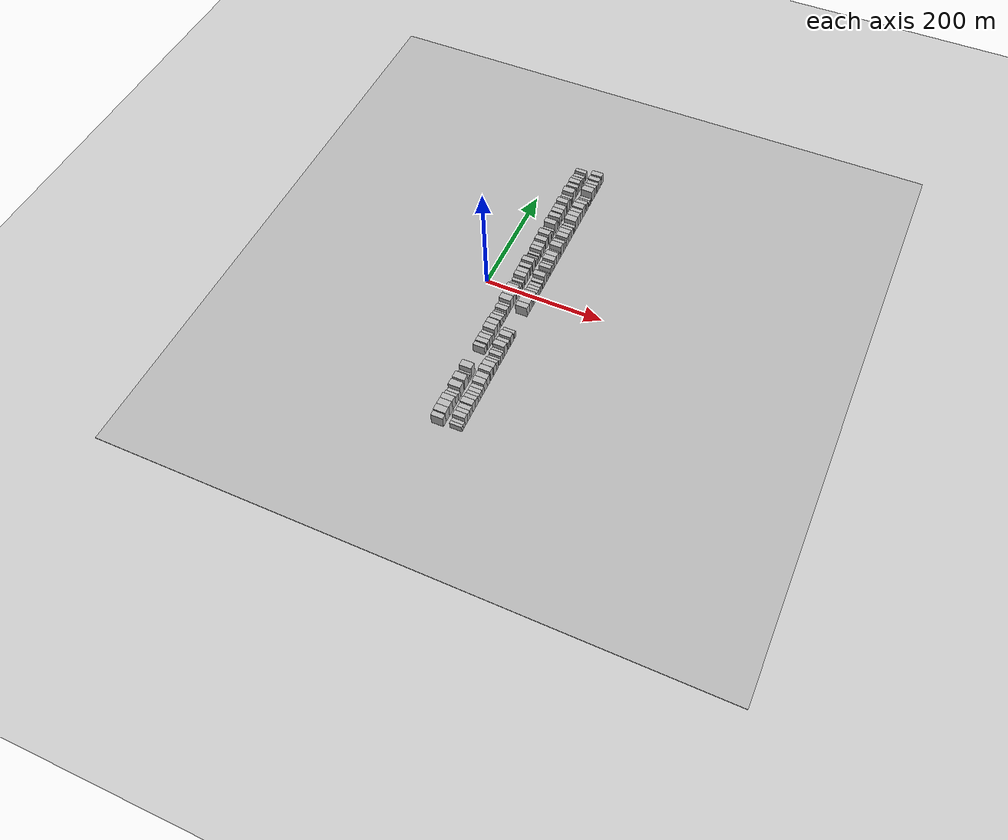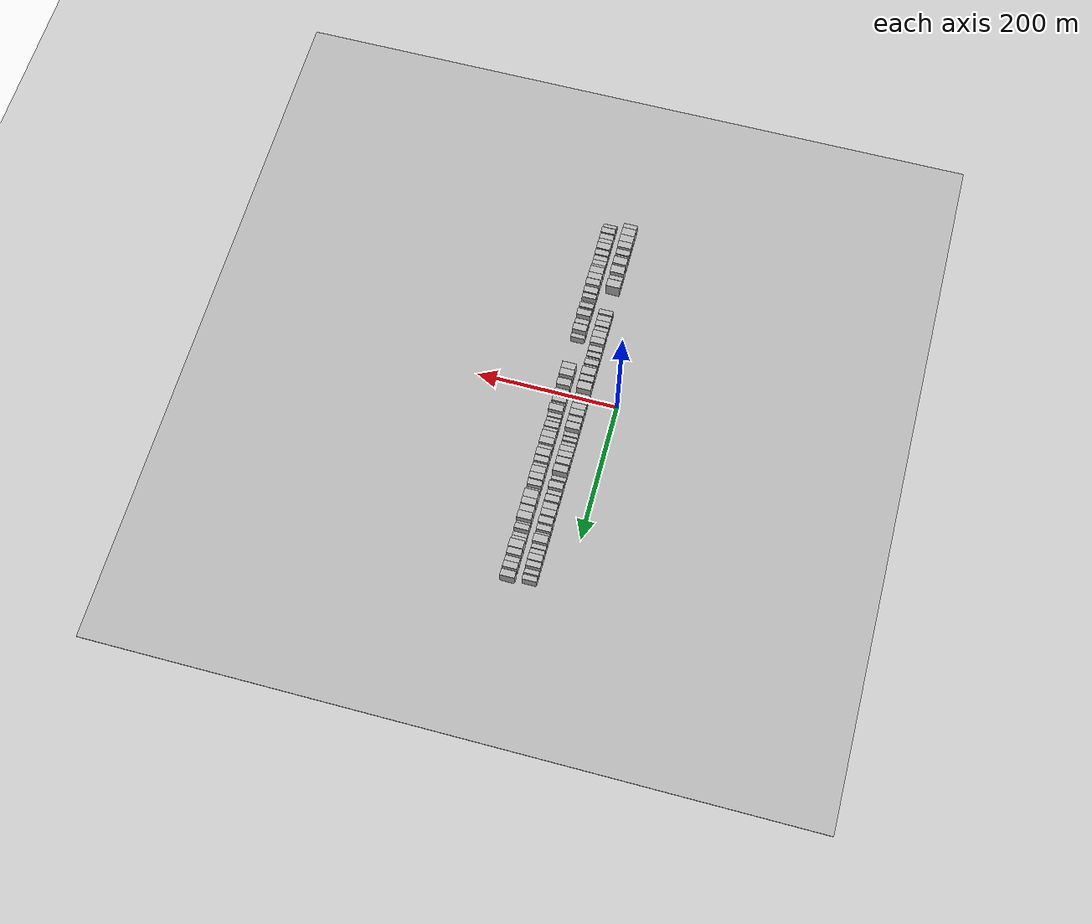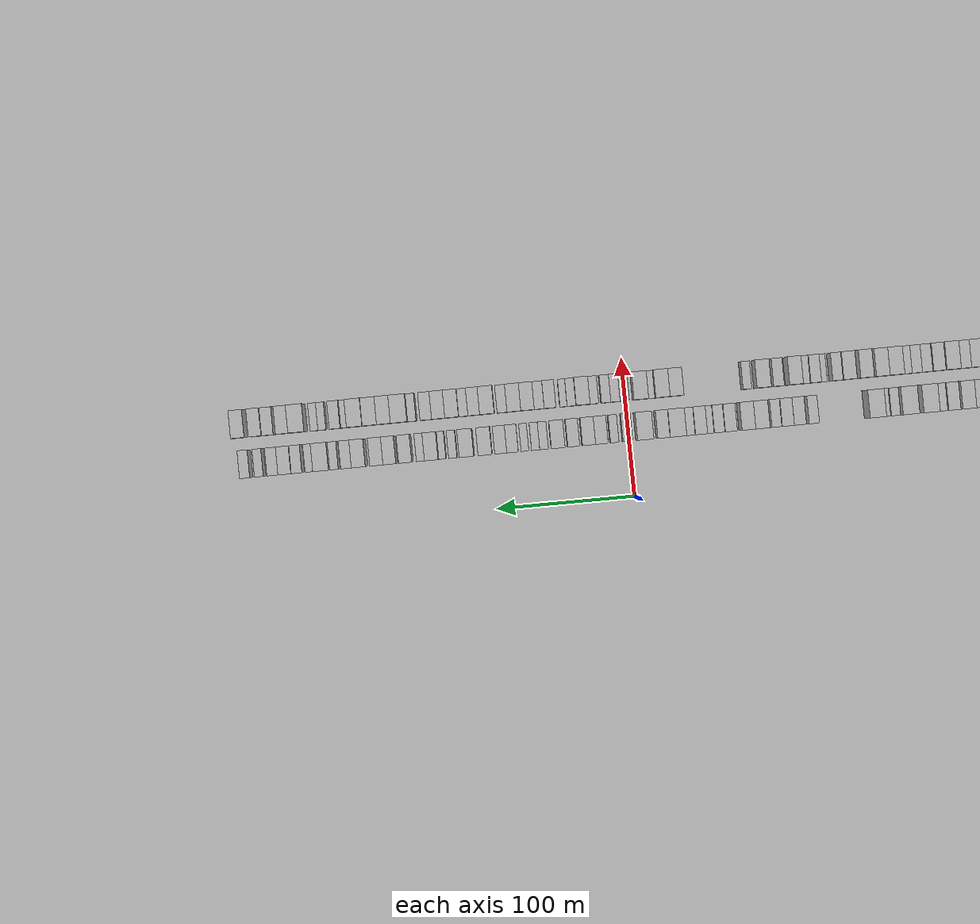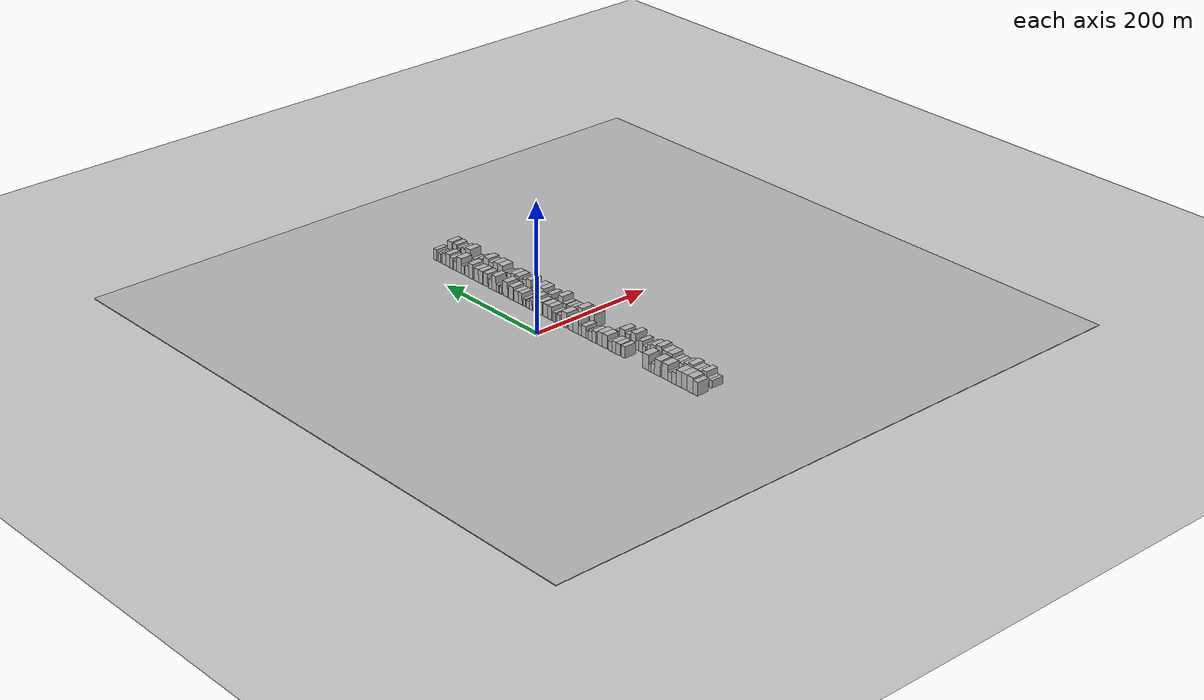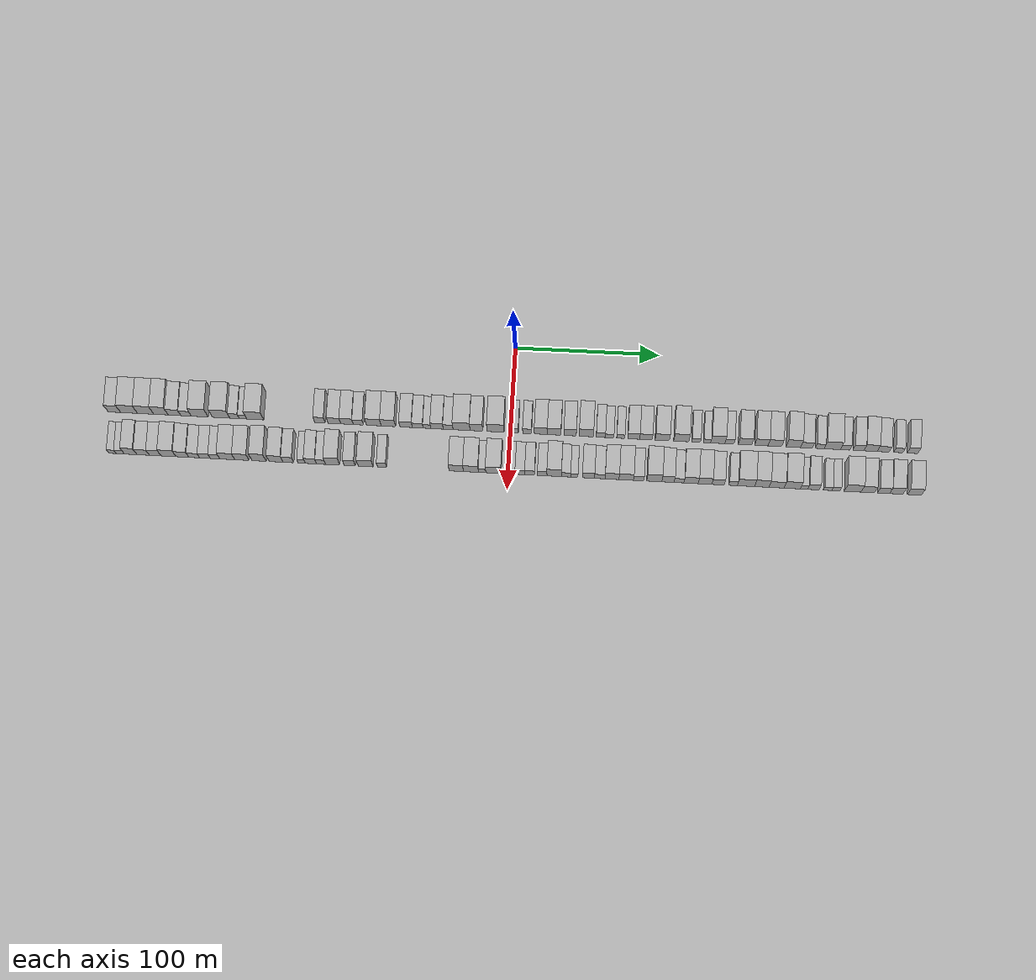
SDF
<?xml version="1.0" encoding="utf-8"?>

<sdf version="1.6">

   <world name="default">

      <gui fullscreen="0">

         <camera name="user_camera">

            <pose>-15 0 4.57585 0 0 0</pose>

            <view_controller>orbit</view_controller>

         </camera>

      </gui>

      <scene>

         <sky>

           <clouds>

             <speed>12</speed>

           </clouds>

         </sky>

         <ambient>0.4 0.4 0.4 1</ambient>

         <background>0.7 0.7 0.7 1</background>

         <shadows>1</shadows>

      </scene>

      <gravity>0 0 -9.8066</gravity>

      <magnetic_field>6e-06 2.3e-05 -4.2e-05</magnetic_field>

      <physics default="0" name="default_physics" type="ode">

         <ode>

            <solver>

               <type>quick</type>

               <iters>10</iters>

               <sor>1.0</sor>

               <use_dynamic_moi_rescaling>0</use_dynamic_moi_rescaling>

            </solver>

            <constraints>

               <cfm>0</cfm>

               <erp>0.2</erp>

               <contact_max_correcting_vel>100</contact_max_correcting_vel>

               <contact_surface_layer>0.001</contact_surface_layer>

            </constraints>

         </ode>

         <max_step_size>0.004</max_step_size>

         <real_time_factor>1</real_time_factor>

         <real_time_update_rate>250</real_time_update_rate>

      </physics>

      <light name="sun" type="directional">

         <cast_shadows>1</cast_shadows>

         <pose>0 0 10 0 0 0</pose>

         <diffuse>0.8 0.8 0.8 1</diffuse>

         <specular>0.2 0.2 0.2 1</specular>

         <attenuation>

            <range>1000</range>

            <constant>0.9</constant>

            <linear>0.01</linear>

            <quadratic>0.001</quadratic>

         </attenuation>

         <direction>-0.5 0.1 -0.9</direction>

      </light>

      <include>

         <name>ground_plane_1</name>

         <uri>model://HANNAS_ground_plane</uri>

         <pose>0 0 0  0 0 0</pose>

      </include>

      <include>

         <name>ground_plane_2</name>

         <uri>model://HANNAS_ground_plane</uri>

         <pose>100 0 0  0 0 0</pose>

      </include>

      <model name="building_1">

         <static>1</static>

         <pose frame="">50.0000 -273.6800 0 0.000000 0.000000 0.000000</pose>

         <link name="link">

            <pose frame="">0 0 10.50 0 0 0</pose>

            <collision name="collision">

               <geometry>

                  <box>

                     <size>20.0000 8.6399 21.0000</size>

                  </box>

               </geometry>

               <max_contacts>10</max_contacts>

               <surface>

                  <contact>

                     <ode/>

                  </contact>

                  <bounce/>

                  <friction>

                     <torsional>

                        <ode/>

                     </torsional>

                     <ode/>

                  </friction>

               </surface>

            </collision>

            <visual name="visual">

               <cast_shadows>0</cast_shadows>

               <geometry>

                  <box>

                     <size>20.0000 8.6399 21.0000</size>

                  </box>

               </geometry>

               <material>

                  <script>

                     <uri>model://HANNAS_wall/materials/scripts</uri>

                     <uri>model://HANNAS_wall/materials/textures</uri>

                     <name>vrc/HANNAS_wall</name>

                  </script>

               </material>

            </visual>

            <self_collide>0</self_collide>

            <enable_wind>0</enable_wind>

            <kinematic>0</kinematic>

         </link>

      </model>

      <model name="building_2">

         <static>1</static>

         <pose frame="">50.0000 -263.5427 0 0.000000 0.000000 0.000000</pose>

         <link name="link">

            <pose frame="">0 0 12.00 0 0 0</pose>

            <collision name="collision">

               <geometry>

                  <box>

                     <size>20.0000 11.6347 24.0000</size>

                  </box>

               </geometry>

               <max_contacts>10</max_contacts>

               <surface>

                  <contact>

                     <ode/>

                  </contact>

                  <bounce/>

                  <friction>

                     <torsional>

                        <ode/>

                     </torsional>

                     <ode/>

                  </friction>

               </surface>

            </collision>

            <visual name="visual">

               <cast_shadows>0</cast_shadows>

               <geometry>

                  <box>

                     <size>20.0000 11.6347 24.0000</size>

                  </box>

               </geometry>

               <material>

                  <script>

                     <uri>model://HANNAS_wall/materials/scripts</uri>

                     <uri>model://HANNAS_wall/materials/textures</uri>

                     <name>vrc/HANNAS_wall</name>

                  </script>

               </material>

            </visual>

            <self_collide>0</self_collide>

            <enable_wind>0</enable_wind>

            <kinematic>0</kinematic>

         </link>

      </model>

      <model name="building_3">

         <static>1</static>

         <pose frame="">50.0000 -252.1240 0 0.000000 0.000000 0.000000</pose>

         <link name="link">

            <pose frame="">0 0 12.00 0 0 0</pose>

            <collision name="collision">

               <geometry>

                  <box>

                     <size>20.0000 11.2028 24.0000</size>

                  </box>

               </geometry>

               <max_contacts>10</max_contacts>

               <surface>

                  <contact>

                     <ode/>

                  </contact>

                  <bounce/>

                  <friction>

                     <torsional>

                        <ode/>

                     </torsional>

                     <ode/>

                  </friction>

               </surface>

            </collision>

            <visual name="visual">

               <cast_shadows>0</cast_shadows>

               <geometry>

                  <box>

                     <size>20.0000 11.2028 24.0000</size>

                  </box>

               </geometry>

               <material>

                  <script>

                     <uri>model://HANNAS_wall/materials/scripts</uri>

                     <uri>model://HANNAS_wall/materials/textures</uri>

                     <name>vrc/HANNAS_wall</name>

                  </script>

               </material>

            </visual>

            <self_collide>0</self_collide>

            <enable_wind>0</enable_wind>

            <kinematic>0</kinematic>

         </link>

      </model>

      <model name="building_4">

         <static>1</static>

         <pose frame="">50.0000 -241.5626 0 0.000000 0.000000 0.000000</pose>

         <link name="link">

            <pose frame="">0 0 12.00 0 0 0</pose>

            <collision name="collision">

               <geometry>

                  <box>

                     <size>20.0000 9.9202 24.0000</size>

                  </box>

               </geometry>

               <max_contacts>10</max_contacts>

               <surface>

                  <contact>

                     <ode/>

                  </contact>

                  <bounce/>

                  <friction>

                     <torsional>

                        <ode/>

                     </torsional>

                     <ode/>

                  </friction>

               </surface>

            </collision>

            <visual name="visual">

               <cast_shadows>0</cast_shadows>

               <geometry>

                  <box>

                     <size>20.0000 9.9202 24.0000</size>

                  </box>

               </geometry>

               <material>

                  <script>

                     <uri>model://HANNAS_wall/materials/scripts</uri>

                     <uri>model://HANNAS_wall/materials/textures</uri>

                     <name>vrc/HANNAS_wall</name>

                  </script>

               </material>

            </visual>

            <self_collide>0</self_collide>

            <enable_wind>0</enable_wind>

            <kinematic>0</kinematic>

         </link>

      </model>

      <model name="building_5">

         <static>1</static>

         <pose frame="">50.0000 -232.2219 0 0.000000 0.000000 0.000000</pose>

         <link name="link">

            <pose frame="">0 0 9.00 0 0 0</pose>

            <collision name="collision">

               <geometry>

                  <box>

                     <size>20.0000 8.7611 18.0000</size>

                  </box>

               </geometry>

               <max_contacts>10</max_contacts>

               <surface>

                  <contact>

                     <ode/>

                  </contact>

                  <bounce/>

                  <friction>

                     <torsional>

                        <ode/>

                     </torsional>

                     <ode/>

                  </friction>

               </surface>

            </collision>

            <visual name="visual">

               <cast_shadows>0</cast_shadows>

               <geometry>

                  <box>

                     <size>20.0000 8.7611 18.0000</size>

                  </box>

               </geometry>

               <material>

                  <script>

                     <uri>model://HANNAS_wall/materials/scripts</uri>

                     <uri>model://HANNAS_wall/materials/textures</uri>

                     <name>vrc/HANNAS_wall</name>

                  </script>

               </material>

            </visual>

            <self_collide>0</self_collide>

            <enable_wind>0</enable_wind>

            <kinematic>0</kinematic>

         </link>

      </model>

      <model name="building_6">

         <static>1</static>

         <pose frame="">50.0000 -224.1485 0 0.000000 0.000000 0.000000</pose>

         <link name="link">

            <pose frame="">0 0 7.50 0 0 0</pose>

            <collision name="collision">

               <geometry>

                  <box>

                     <size>20.0000 7.3857 15.0000</size>

                  </box>

               </geometry>

               <max_contacts>10</max_contacts>

               <surface>

                  <contact>

                     <ode/>

                  </contact>

                  <bounce/>

                  <friction>

                     <torsional>

                        <ode/>

                     </torsional>

                     <ode/>

                  </friction>

               </surface>

            </collision>

            <visual name="visual">

               <cast_shadows>0</cast_shadows>

               <geometry>

                  <box>

                     <size>20.0000 7.3857 15.0000</size>

                  </box>

               </geometry>

               <material>

                  <script>

                     <uri>model://HANNAS_wall/materials/scripts</uri>

                     <uri>model://HANNAS_wall/materials/textures</uri>

                     <name>vrc/HANNAS_wall</name>

                  </script>

               </material>

            </visual>

            <self_collide>0</self_collide>

            <enable_wind>0</enable_wind>

            <kinematic>0</kinematic>

         </link>

      </model>

      <model name="building_7">

         <static>1</static>

         <pose frame="">50.0000 -214.6706 0 0.000000 0.000000 0.000000</pose>

         <link name="link">

            <pose frame="">0 0 12.00 0 0 0</pose>

            <collision name="collision">

               <geometry>

                  <box>

                     <size>20.0000 11.5701 24.0000</size>

                  </box>

               </geometry>

               <max_contacts>10</max_contacts>

               <surface>

                  <contact>

                     <ode/>

                  </contact>

                  <bounce/>

                  <friction>

                     <torsional>

                        <ode/>

                     </torsional>

                     <ode/>

                  </friction>

               </surface>

            </collision>

            <visual name="visual">

               <cast_shadows>0</cast_shadows>

               <geometry>

                  <box>

                     <size>20.0000 11.5701 24.0000</size>

                  </box>

               </geometry>

               <material>

                  <script>

                     <uri>model://HANNAS_wall/materials/scripts</uri>

                     <uri>model://HANNAS_wall/materials/textures</uri>

                     <name>vrc/HANNAS_wall</name>

                  </script>

               </material>

            </visual>

            <self_collide>0</self_collide>

            <enable_wind>0</enable_wind>

            <kinematic>0</kinematic>

         </link>

      </model>

      <model name="building_8">

         <static>1</static>

         <pose frame="">50.0000 -199.9398 0 0.000000 0.000000 0.000000</pose>

         <link name="link">

            <pose frame="">0 0 12.00 0 0 0</pose>

            <collision name="collision">

               <geometry>

                  <box>

                     <size>20.0000 11.8915 24.0000</size>

                  </box>

               </geometry>

               <max_contacts>10</max_contacts>

               <surface>

                  <contact>

                     <ode/>

                  </contact>

                  <bounce/>

                  <friction>

                     <torsional>

                        <ode/>

                     </torsional>

                     <ode/>

                  </friction>

               </surface>

            </collision>

            <visual name="visual">

               <cast_shadows>0</cast_shadows>

               <geometry>

                  <box>

                     <size>20.0000 11.8915 24.0000</size>

                  </box>

               </geometry>

               <material>

                  <script>

                     <uri>model://HANNAS_wall/materials/scripts</uri>

                     <uri>model://HANNAS_wall/materials/textures</uri>

                     <name>vrc/HANNAS_wall</name>

                  </script>

               </material>

            </visual>

            <self_collide>0</self_collide>

            <enable_wind>0</enable_wind>

            <kinematic>0</kinematic>

         </link>

      </model>

      <model name="building_9">

         <static>1</static>

         <pose frame="">50.0000 -190.6809 0 0.000000 0.000000 0.000000</pose>

         <link name="link">

            <pose frame="">0 0 7.50 0 0 0</pose>

            <collision name="collision">

               <geometry>

                  <box>

                     <size>20.0000 6.6264 15.0000</size>

                  </box>

               </geometry>

               <max_contacts>10</max_contacts>

               <surface>

                  <contact>

                     <ode/>

                  </contact>

                  <bounce/>

                  <friction>

                     <torsional>

                        <ode/>

                     </torsional>

                     <ode/>

                  </friction>

               </surface>

            </collision>

            <visual name="visual">

               <cast_shadows>0</cast_shadows>

               <geometry>

                  <box>

                     <size>20.0000 6.6264 15.0000</size>

                  </box>

               </geometry>

               <material>

                  <script>

                     <uri>model://HANNAS_wall/materials/scripts</uri>

                     <uri>model://HANNAS_wall/materials/textures</uri>

                     <name>vrc/HANNAS_wall</name>

                  </script>

               </material>

            </visual>

            <self_collide>0</self_collide>

            <enable_wind>0</enable_wind>

            <kinematic>0</kinematic>

         </link>

      </model>

      <model name="building_10">

         <static>1</static>

         <pose frame="">50.0000 -184.7908 0 0.000000 0.000000 0.000000</pose>

         <link name="link">

            <pose frame="">0 0 6.00 0 0 0</pose>

            <collision name="collision">

               <geometry>

                  <box>

                     <size>20.0000 5.1538 12.0000</size>

                  </box>

               </geometry>

               <max_contacts>10</max_contacts>

               <surface>

                  <contact>

                     <ode/>

                  </contact>

                  <bounce/>

                  <friction>

                     <torsional>

                        <ode/>

                     </torsional>

                     <ode/>

                  </friction>

               </surface>

            </collision>

            <visual name="visual">

               <cast_shadows>0</cast_shadows>

               <geometry>

                  <box>

                     <size>20.0000 5.1538 12.0000</size>

                  </box>

               </geometry>

               <material>

                  <script>

                     <uri>model://HANNAS_wall/materials/scripts</uri>

                     <uri>model://HANNAS_wall/materials/textures</uri>

                     <name>vrc/HANNAS_wall</name>

                  </script>

               </material>

            </visual>

            <self_collide>0</self_collide>

            <enable_wind>0</enable_wind>

            <kinematic>0</kinematic>

         </link>

      </model>

      <model name="building_11">

         <static>1</static>

         <pose frame="">50.0000 -176.3409 0 0.000000 0.000000 0.000000</pose>

         <link name="link">

            <pose frame="">0 0 12.00 0 0 0</pose>

            <collision name="collision">

               <geometry>

                  <box>

                     <size>20.0000 11.7459 24.0000</size>

                  </box>

               </geometry>

               <max_contacts>10</max_contacts>

               <surface>

                  <contact>

                     <ode/>

                  </contact>

                  <bounce/>

                  <friction>

                     <torsional>

                        <ode/>

                     </torsional>

                     <ode/>

                  </friction>

               </surface>

            </collision>

            <visual name="visual">

               <cast_shadows>0</cast_shadows>

               <geometry>

                  <box>

                     <size>20.0000 11.7459 24.0000</size>

                  </box>

               </geometry>

               <material>

                  <script>

                     <uri>model://HANNAS_wall/materials/scripts</uri>

                     <uri>model://HANNAS_wall/materials/textures</uri>

                     <name>vrc/HANNAS_wall</name>

                  </script>

               </material>

            </visual>

            <self_collide>0</self_collide>

            <enable_wind>0</enable_wind>

            <kinematic>0</kinematic>

         </link>

      </model>

      <model name="building_12">

         <static>1</static>

         <pose frame="">50.0000 -131.5599 0 0.000000 0.000000 0.000000</pose>

         <link name="link">

            <pose frame="">0 0 9.00 0 0 0</pose>

            <collision name="collision">

               <geometry>

                  <box>

                     <size>20.0000 7.2720 18.0000</size>

                  </box>

               </geometry>

               <max_contacts>10</max_contacts>

               <surface>

                  <contact>

                     <ode/>

                  </contact>

                  <bounce/>

                  <friction>

                     <torsional>

                        <ode/>

                     </torsional>

                     <ode/>

                  </friction>

               </surface>

            </collision>

            <visual name="visual">

               <cast_shadows>0</cast_shadows>

               <geometry>

                  <box>

                     <size>20.0000 7.2720 18.0000</size>

                  </box>

               </geometry>

               <material>

                  <script>

                     <uri>model://HANNAS_wall/materials/scripts</uri>

                     <uri>model://HANNAS_wall/materials/textures</uri>

                     <name>vrc/HANNAS_wall</name>

                  </script>

               </material>

            </visual>

            <self_collide>0</self_collide>

            <enable_wind>0</enable_wind>

            <kinematic>0</kinematic>

         </link>

      </model>

      <model name="building_13">

         <static>1</static>

         <pose frame="">50.0000 -121.6003 0 0.000000 0.000000 0.000000</pose>

         <link name="link">

            <pose frame="">0 0 9.00 0 0 0</pose>

            <collision name="collision">

               <geometry>

                  <box>

                     <size>20.0000 8.6473 18.0000</size>

                  </box>

               </geometry>

               <max_contacts>10</max_contacts>

               <surface>

                  <contact>

                     <ode/>

                  </contact>

                  <bounce/>

                  <friction>

                     <torsional>

                        <ode/>

                     </torsional>

                     <ode/>

                  </friction>

               </surface>

            </collision>

            <visual name="visual">

               <cast_shadows>0</cast_shadows>

               <geometry>

                  <box>

                     <size>20.0000 8.6473 18.0000</size>

                  </box>

               </geometry>

               <material>

                  <script>

                     <uri>model://HANNAS_wall/materials/scripts</uri>

                     <uri>model://HANNAS_wall/materials/textures</uri>

                     <name>vrc/HANNAS_wall</name>

                  </script>

               </material>

            </visual>

            <self_collide>0</self_collide>

            <enable_wind>0</enable_wind>

            <kinematic>0</kinematic>

         </link>

      </model>

      <model name="building_14">

         <static>1</static>

         <pose frame="">50.0000 -112.9664 0 0.000000 0.000000 0.000000</pose>

         <link name="link">

            <pose frame="">0 0 9.00 0 0 0</pose>

            <collision name="collision">

               <geometry>

                  <box>

                     <size>20.0000 8.6204 18.0000</size>

                  </box>

               </geometry>

               <max_contacts>10</max_contacts>

               <surface>

                  <contact>

                     <ode/>

                  </contact>

                  <bounce/>

                  <friction>

                     <torsional>

                        <ode/>

                     </torsional>

                     <ode/>

                  </friction>

               </surface>

            </collision>

            <visual name="visual">

               <cast_shadows>0</cast_shadows>

               <geometry>

                  <box>

                     <size>20.0000 8.6204 18.0000</size>

                  </box>

               </geometry>

               <material>

                  <script>

                     <uri>model://HANNAS_wall/materials/scripts</uri>

                     <uri>model://HANNAS_wall/materials/textures</uri>

                     <name>vrc/HANNAS_wall</name>

                  </script>

               </material>

            </visual>

            <self_collide>0</self_collide>

            <enable_wind>0</enable_wind>

            <kinematic>0</kinematic>

         </link>

      </model>

      <model name="building_15">

         <static>1</static>

         <pose frame="">50.0000 -105.1115 0 0.000000 0.000000 0.000000</pose>

         <link name="link">

            <pose frame="">0 0 7.50 0 0 0</pose>

            <collision name="collision">

               <geometry>

                  <box>

                     <size>20.0000 7.0894 15.0000</size>

                  </box>

               </geometry>

               <max_contacts>10</max_contacts>

               <surface>

                  <contact>

                     <ode/>

                  </contact>

                  <bounce/>

                  <friction>

                     <torsional>

                        <ode/>

                     </torsional>

                     <ode/>

                  </friction>

               </surface>

            </collision>

            <visual name="visual">

               <cast_shadows>0</cast_shadows>

               <geometry>

                  <box>

                     <size>20.0000 7.0894 15.0000</size>

                  </box>

               </geometry>

               <material>

                  <script>

                     <uri>model://HANNAS_wall/materials/scripts</uri>

                     <uri>model://HANNAS_wall/materials/textures</uri>

                     <name>vrc/HANNAS_wall</name>

                  </script>

               </material>

            </visual>

            <self_collide>0</self_collide>

            <enable_wind>0</enable_wind>

            <kinematic>0</kinematic>

         </link>

      </model>

      <model name="building_16">

         <static>1</static>

         <pose frame="">50.0000 -94.4157 0 0.000000 0.000000 0.000000</pose>

         <link name="link">

            <pose frame="">0 0 10.50 0 0 0</pose>

            <collision name="collision">

               <geometry>

                  <box>

                     <size>20.0000 10.3022 21.0000</size>

                  </box>

               </geometry>

               <max_contacts>10</max_contacts>

               <surface>

                  <contact>

                     <ode/>

                  </contact>

                  <bounce/>

                  <friction>

                     <torsional>

                        <ode/>

                     </torsional>

                     <ode/>

                  </friction>

               </surface>

            </collision>

            <visual name="visual">

               <cast_shadows>0</cast_shadows>

               <geometry>

                  <box>

                     <size>20.0000 10.3022 21.0000</size>

                  </box>

               </geometry>

               <material>

                  <script>

                     <uri>model://HANNAS_wall/materials/scripts</uri>

                     <uri>model://HANNAS_wall/materials/textures</uri>

                     <name>vrc/HANNAS_wall</name>

                  </script>

               </material>

            </visual>

            <self_collide>0</self_collide>

            <enable_wind>0</enable_wind>

            <kinematic>0</kinematic>

         </link>

      </model>

      <model name="building_17">

         <static>1</static>

         <pose frame="">50.0000 -84.3508 0 0.000000 0.000000 0.000000</pose>

         <link name="link">

            <pose frame="">0 0 10.50 0 0 0</pose>

            <collision name="collision">

               <geometry>

                  <box>

                     <size>20.0000 9.8277 21.0000</size>

                  </box>

               </geometry>

               <max_contacts>10</max_contacts>

               <surface>

                  <contact>

                     <ode/>

                  </contact>

                  <bounce/>

                  <friction>

                     <torsional>

                        <ode/>

                     </torsional>

                     <ode/>

                  </friction>

               </surface>

            </collision>

            <visual name="visual">

               <cast_shadows>0</cast_shadows>

               <geometry>

                  <box>

                     <size>20.0000 9.8277 21.0000</size>

                  </box>

               </geometry>

               <material>

                  <script>

                     <uri>model://HANNAS_wall/materials/scripts</uri>

                     <uri>model://HANNAS_wall/materials/textures</uri>

                     <name>vrc/HANNAS_wall</name>

                  </script>

               </material>

            </visual>

            <self_collide>0</self_collide>

            <enable_wind>0</enable_wind>

            <kinematic>0</kinematic>

         </link>

      </model>

      <model name="building_18">

         <static>1</static>

         <pose frame="">50.0000 -72.1331 0 0.000000 0.000000 0.000000</pose>

         <link name="link">

            <pose frame="">0 0 9.00 0 0 0</pose>

            <collision name="collision">

               <geometry>

                  <box>

                     <size>20.0000 8.6077 18.0000</size>

                  </box>

               </geometry>

               <max_contacts>10</max_contacts>

               <surface>

                  <contact>

                     <ode/>

                  </contact>

                  <bounce/>

                  <friction>

                     <torsional>

                        <ode/>

                     </torsional>

                     <ode/>

                  </friction>

               </surface>

            </collision>

            <visual name="visual">

               <cast_shadows>0</cast_shadows>

               <geometry>

                  <box>

                     <size>20.0000 8.6077 18.0000</size>

                  </box>

               </geometry>

               <material>

                  <script>

                     <uri>model://HANNAS_wall/materials/scripts</uri>

                     <uri>model://HANNAS_wall/materials/textures</uri>

                     <name>vrc/HANNAS_wall</name>

                  </script>

               </material>

            </visual>

            <self_collide>0</self_collide>

            <enable_wind>0</enable_wind>

            <kinematic>0</kinematic>

         </link>

      </model>

      <model name="building_19">

         <static>1</static>

         <pose frame="">50.0000 -64.0873 0 0.000000 0.000000 0.000000</pose>

         <link name="link">

            <pose frame="">0 0 7.50 0 0 0</pose>

            <collision name="collision">

               <geometry>

                  <box>

                     <size>20.0000 7.4838 15.0000</size>

                  </box>

               </geometry>

               <max_contacts>10</max_contacts>

               <surface>

                  <contact>

                     <ode/>

                  </contact>

                  <bounce/>

                  <friction>

                     <torsional>

                        <ode/>

                     </torsional>

                     <ode/>

                  </friction>

               </surface>

            </collision>

            <visual name="visual">

               <cast_shadows>0</cast_shadows>

               <geometry>

                  <box>

                     <size>20.0000 7.4838 15.0000</size>

                  </box>

               </geometry>

               <material>

                  <script>

                     <uri>model://HANNAS_wall/materials/scripts</uri>

                     <uri>model://HANNAS_wall/materials/textures</uri>

                     <name>vrc/HANNAS_wall</name>

                  </script>

               </material>

            </visual>

            <self_collide>0</self_collide>

            <enable_wind>0</enable_wind>

            <kinematic>0</kinematic>

         </link>

      </model>

      <model name="building_20">

         <static>1</static>

         <pose frame="">50.0000 -57.7232 0 0.000000 0.000000 0.000000</pose>

         <link name="link">

            <pose frame="">0 0 6.00 0 0 0</pose>

            <collision name="collision">

               <geometry>

                  <box>

                     <size>20.0000 5.2445 12.0000</size>

                  </box>

               </geometry>

               <max_contacts>10</max_contacts>

               <surface>

                  <contact>

                     <ode/>

                  </contact>

                  <bounce/>

                  <friction>

                     <torsional>

                        <ode/>

                     </torsional>

                     <ode/>

                  </friction>

               </surface>

            </collision>

            <visual name="visual">

               <cast_shadows>0</cast_shadows>

               <geometry>

                  <box>

                     <size>20.0000 5.2445 12.0000</size>

                  </box>

               </geometry>

               <material>

                  <script>

                     <uri>model://HANNAS_wall/materials/scripts</uri>

                     <uri>model://HANNAS_wall/materials/textures</uri>

                     <name>vrc/HANNAS_wall</name>

                  </script>

               </material>

            </visual>

            <self_collide>0</self_collide>

            <enable_wind>0</enable_wind>

            <kinematic>0</kinematic>

         </link>

      </model>

      <model name="building_21">

         <static>1</static>

         <pose frame="">50.0000 -50.7852 0 0.000000 0.000000 0.000000</pose>

         <link name="link">

            <pose frame="">0 0 9.00 0 0 0</pose>

            <collision name="collision">

               <geometry>

                  <box>

                     <size>20.0000 8.6315 18.0000</size>

                  </box>

               </geometry>

               <max_contacts>10</max_contacts>

               <surface>

                  <contact>

                     <ode/>

                  </contact>

                  <bounce/>

                  <friction>

                     <torsional>

                        <ode/>

                     </torsional>

                     <ode/>

                  </friction>

               </surface>

            </collision>

            <visual name="visual">

               <cast_shadows>0</cast_shadows>

               <geometry>

                  <box>

                     <size>20.0000 8.6315 18.0000</size>

                  </box>

               </geometry>

               <material>

                  <script>

                     <uri>model://HANNAS_wall/materials/scripts</uri>

                     <uri>model://HANNAS_wall/materials/textures</uri>

                     <name>vrc/HANNAS_wall</name>

                  </script>

               </material>

            </visual>

            <self_collide>0</self_collide>

            <enable_wind>0</enable_wind>

            <kinematic>0</kinematic>

         </link>

      </model>

      <model name="building_22">

         <static>1</static>

         <pose frame="">50.0000 -43.0799 0 0.000000 0.000000 0.000000</pose>

         <link name="link">

            <pose frame="">0 0 7.50 0 0 0</pose>

            <collision name="collision">

               <geometry>

                  <box>

                     <size>20.0000 6.7789 15.0000</size>

                  </box>

               </geometry>

               <max_contacts>10</max_contacts>

               <surface>

                  <contact>

                     <ode/>

                  </contact>

                  <bounce/>

                  <friction>

                     <torsional>

                        <ode/>

                     </torsional>

                     <ode/>

                  </friction>

               </surface>

            </collision>

            <visual name="visual">

               <cast_shadows>0</cast_shadows>

               <geometry>

                  <box>

                     <size>20.0000 6.7789 15.0000</size>

                  </box>

               </geometry>

               <material>

                  <script>

                     <uri>model://HANNAS_wall/materials/scripts</uri>

                     <uri>model://HANNAS_wall/materials/textures</uri>

                     <name>vrc/HANNAS_wall</name>

                  </script>

               </material>

            </visual>

            <self_collide>0</self_collide>

            <enable_wind>0</enable_wind>

            <kinematic>0</kinematic>

         </link>

      </model>

      <model name="building_23">

         <static>1</static>

         <pose frame="">50.0000 -33.8264 0 0.000000 0.000000 0.000000</pose>

         <link name="link">

            <pose frame="">0 0 12.00 0 0 0</pose>

            <collision name="collision">

               <geometry>

                  <box>

                     <size>20.0000 11.7282 24.0000</size>

                  </box>

               </geometry>

               <max_contacts>10</max_contacts>

               <surface>

                  <contact>

                     <ode/>

                  </contact>

                  <bounce/>

                  <friction>

                     <torsional>

                        <ode/>

                     </torsional>

                     <ode/>

                  </friction>

               </surface>

            </collision>

            <visual name="visual">

               <cast_shadows>0</cast_shadows>

               <geometry>

                  <box>

                     <size>20.0000 11.7282 24.0000</size>

                  </box>

               </geometry>

               <material>

                  <script>

                     <uri>model://HANNAS_wall/materials/scripts</uri>

                     <uri>model://HANNAS_wall/materials/textures</uri>

                     <name>vrc/HANNAS_wall</name>

                  </script>

               </material>

            </visual>

            <self_collide>0</self_collide>

            <enable_wind>0</enable_wind>

            <kinematic>0</kinematic>

         </link>

      </model>

      <model name="building_24">

         <static>1</static>

         <pose frame="">50.0000 -23.6046 0 0.000000 0.000000 0.000000</pose>

         <link name="link">

            <pose frame="">0 0 10.50 0 0 0</pose>

            <collision name="collision">

               <geometry>

                  <box>

                     <size>20.0000 8.7154 21.0000</size>

                  </box>

               </geometry>

               <max_contacts>10</max_contacts>

               <surface>

                  <contact>

                     <ode/>

                  </contact>

                  <bounce/>

                  <friction>

                     <torsional>

                        <ode/>

                     </torsional>

                     <ode/>

                  </friction>

               </surface>

            </collision>

            <visual name="visual">

               <cast_shadows>0</cast_shadows>

               <geometry>

                  <box>

                     <size>20.0000 8.7154 21.0000</size>

                  </box>

               </geometry>

               <material>

                  <script>

                     <uri>model://HANNAS_wall/materials/scripts</uri>

                     <uri>model://HANNAS_wall/materials/textures</uri>

                     <name>vrc/HANNAS_wall</name>

                  </script>

               </material>

            </visual>

            <self_collide>0</self_collide>

            <enable_wind>0</enable_wind>

            <kinematic>0</kinematic>

         </link>

      </model>

      <model name="building_25">

         <static>1</static>

         <pose frame="">50.0000 -10.4218 0 0.000000 0.000000 0.000000</pose>

         <link name="link">

            <pose frame="">0 0 12.00 0 0 0</pose>

            <collision name="collision">

               <geometry>

                  <box>

                     <size>20.0000 11.6502 24.0000</size>

                  </box>

               </geometry>

               <max_contacts>10</max_contacts>

               <surface>

                  <contact>

                     <ode/>

                  </contact>

                  <bounce/>

                  <friction>

                     <torsional>

                        <ode/>

                     </torsional>

                     <ode/>

                  </friction>

               </surface>

            </collision>

            <visual name="visual">

               <cast_shadows>0</cast_shadows>

               <geometry>

                  <box>

                     <size>20.0000 11.6502 24.0000</size>

                  </box>

               </geometry>

               <material>

                  <script>

                     <uri>model://HANNAS_wall/materials/scripts</uri>

                     <uri>model://HANNAS_wall/materials/textures</uri>

                     <name>vrc/HANNAS_wall</name>

                  </script>

               </material>

            </visual>

            <self_collide>0</self_collide>

            <enable_wind>0</enable_wind>

            <kinematic>0</kinematic>

         </link>

      </model>

      <model name="building_26">

         <static>1</static>

         <pose frame="">50.0000 1.8205 0 0.000000 0.000000 0.000000</pose>

         <link name="link">

            <pose frame="">0 0 7.50 0 0 0</pose>

            <collision name="collision">

               <geometry>

                  <box>

                     <size>20.0000 6.8344 15.0000</size>

                  </box>

               </geometry>

               <max_contacts>10</max_contacts>

               <surface>

                  <contact>

                     <ode/>

                  </contact>

                  <bounce/>

                  <friction>

                     <torsional>

                        <ode/>

                     </torsional>

                     <ode/>

                  </friction>

               </surface>

            </collision>

            <visual name="visual">

               <cast_shadows>0</cast_shadows>

               <geometry>

                  <box>

                     <size>20.0000 6.8344 15.0000</size>

                  </box>

               </geometry>

               <material>

                  <script>

                     <uri>model://HANNAS_wall/materials/scripts</uri>

                     <uri>model://HANNAS_wall/materials/textures</uri>

                     <name>vrc/HANNAS_wall</name>

                  </script>

               </material>

            </visual>

            <self_collide>0</self_collide>

            <enable_wind>0</enable_wind>

            <kinematic>0</kinematic>

         </link>

      </model>

      <model name="building_27">

         <static>1</static>

         <pose frame="">50.0000 11.2494 0 0.000000 0.000000 0.000000</pose>

         <link name="link">

            <pose frame="">0 0 7.50 0 0 0</pose>

            <collision name="collision">

               <geometry>

                  <box>

                     <size>20.0000 6.0233 15.0000</size>

                  </box>

               </geometry>

               <max_contacts>10</max_contacts>

               <surface>

                  <contact>

                     <ode/>

                  </contact>

                  <bounce/>

                  <friction>

                     <torsional>

                        <ode/>

                     </torsional>

                     <ode/>

                  </friction>

               </surface>

            </collision>

            <visual name="visual">

               <cast_shadows>0</cast_shadows>

               <geometry>

                  <box>

                     <size>20.0000 6.0233 15.0000</size>

                  </box>

               </geometry>

               <material>

                  <script>

                     <uri>model://HANNAS_wall/materials/scripts</uri>

                     <uri>model://HANNAS_wall/materials/textures</uri>

                     <name>vrc/HANNAS_wall</name>

                  </script>

               </material>

            </visual>

            <self_collide>0</self_collide>

            <enable_wind>0</enable_wind>

            <kinematic>0</kinematic>

         </link>

      </model>

      <model name="building_28">

         <static>1</static>

         <pose frame="">50.0000 20.7345 0 0.000000 0.000000 0.000000</pose>

         <link name="link">

            <pose frame="">0 0 10.50 0 0 0</pose>

            <collision name="collision">

               <geometry>

                  <box>

                     <size>20.0000 8.9469 21.0000</size>

                  </box>

               </geometry>

               <max_contacts>10</max_contacts>

               <surface>

                  <contact>

                     <ode/>

                  </contact>

                  <bounce/>

                  <friction>

                     <torsional>

                        <ode/>

                     </torsional>

                     <ode/>

                  </friction>

               </surface>

            </collision>

            <visual name="visual">

               <cast_shadows>0</cast_shadows>

               <geometry>

                  <box>

                     <size>20.0000 8.9469 21.0000</size>

                  </box>

               </geometry>

               <material>

                  <script>

                     <uri>model://HANNAS_wall/materials/scripts</uri>

                     <uri>model://HANNAS_wall/materials/textures</uri>

                     <name>vrc/HANNAS_wall</name>

                  </script>

               </material>

            </visual>

            <self_collide>0</self_collide>

            <enable_wind>0</enable_wind>

            <kinematic>0</kinematic>

         </link>

      </model>

      <model name="building_29">

         <static>1</static>

         <pose frame="">50.0000 29.8914 0 0.000000 0.000000 0.000000</pose>

         <link name="link">

            <pose frame="">0 0 10.50 0 0 0</pose>

            <collision name="collision">

               <geometry>

                  <box>

                     <size>20.0000 9.3669 21.0000</size>

                  </box>

               </geometry>

               <max_contacts>10</max_contacts>

               <surface>

                  <contact>

                     <ode/>

                  </contact>

                  <bounce/>

                  <friction>

                     <torsional>

                        <ode/>

                     </torsional>

                     <ode/>

                  </friction>

               </surface>

            </collision>

            <visual name="visual">

               <cast_shadows>0</cast_shadows>

               <geometry>

                  <box>

                     <size>20.0000 9.3669 21.0000</size>

                  </box>

               </geometry>

               <material>

                  <script>

                     <uri>model://HANNAS_wall/materials/scripts</uri>

                     <uri>model://HANNAS_wall/materials/textures</uri>

                     <name>vrc/HANNAS_wall</name>

                  </script>

               </material>

            </visual>

            <self_collide>0</self_collide>

            <enable_wind>0</enable_wind>

            <kinematic>0</kinematic>

         </link>

      </model>

      <model name="building_30">

         <static>1</static>

         <pose frame="">50.0000 40.8445 0 0.000000 0.000000 0.000000</pose>

         <link name="link">

            <pose frame="">0 0 10.50 0 0 0</pose>

            <collision name="collision">

               <geometry>

                  <box>

                     <size>20.0000 8.5393 21.0000</size>

                  </box>

               </geometry>

               <max_contacts>10</max_contacts>

               <surface>

                  <contact>

                     <ode/>

                  </contact>

                  <bounce/>

                  <friction>

                     <torsional>

                        <ode/>

                     </torsional>

                     <ode/>

                  </friction>

               </surface>

            </collision>

            <visual name="visual">

               <cast_shadows>0</cast_shadows>

               <geometry>

                  <box>

                     <size>20.0000 8.5393 21.0000</size>

                  </box>

               </geometry>

               <material>

                  <script>

                     <uri>model://HANNAS_wall/materials/scripts</uri>

                     <uri>model://HANNAS_wall/materials/textures</uri>

                     <name>vrc/HANNAS_wall</name>

                  </script>

               </material>

            </visual>

            <self_collide>0</self_collide>

            <enable_wind>0</enable_wind>

            <kinematic>0</kinematic>

         </link>

      </model>

      <model name="building_31">

         <static>1</static>

         <pose frame="">50.0000 52.0060 0 0.000000 0.000000 0.000000</pose>

         <link name="link">

            <pose frame="">0 0 12.00 0 0 0</pose>

            <collision name="collision">

               <geometry>

                  <box>

                     <size>20.0000 9.7837 24.0000</size>

                  </box>

               </geometry>

               <max_contacts>10</max_contacts>

               <surface>

                  <contact>

                     <ode/>

                  </contact>

                  <bounce/>

                  <friction>

                     <torsional>

                        <ode/>

                     </torsional>

                     <ode/>

                  </friction>

               </surface>

            </collision>

            <visual name="visual">

               <cast_shadows>0</cast_shadows>

               <geometry>

                  <box>

                     <size>20.0000 9.7837 24.0000</size>

                  </box>

               </geometry>

               <material>

                  <script>

                     <uri>model://HANNAS_wall/materials/scripts</uri>

                     <uri>model://HANNAS_wall/materials/textures</uri>

                     <name>vrc/HANNAS_wall</name>

                  </script>

               </material>

            </visual>

            <self_collide>0</self_collide>

            <enable_wind>0</enable_wind>

            <kinematic>0</kinematic>

         </link>

      </model>

      <model name="building_32">

         <static>1</static>

         <pose frame="">50.0000 62.0029 0 0.000000 0.000000 0.000000</pose>

         <link name="link">

            <pose frame="">0 0 7.50 0 0 0</pose>

            <collision name="collision">

               <geometry>

                  <box>

                     <size>20.0000 6.2100 15.0000</size>

                  </box>

               </geometry>

               <max_contacts>10</max_contacts>

               <surface>

                  <contact>

                     <ode/>

                  </contact>

                  <bounce/>

                  <friction>

                     <torsional>

                        <ode/>

                     </torsional>

                     <ode/>

                  </friction>

               </surface>

            </collision>

            <visual name="visual">

               <cast_shadows>0</cast_shadows>

               <geometry>

                  <box>

                     <size>20.0000 6.2100 15.0000</size>

                  </box>

               </geometry>

               <material>

                  <script>

                     <uri>model://HANNAS_wall/materials/scripts</uri>

                     <uri>model://HANNAS_wall/materials/textures</uri>

                     <name>vrc/HANNAS_wall</name>

                  </script>

               </material>

            </visual>

            <self_collide>0</self_collide>

            <enable_wind>0</enable_wind>

            <kinematic>0</kinematic>

         </link>

      </model>

      <model name="building_33">

         <static>1</static>

         <pose frame="">50.0000 68.0399 0 0.000000 0.000000 0.000000</pose>

         <link name="link">

            <pose frame="">0 0 6.00 0 0 0</pose>

            <collision name="collision">

               <geometry>

                  <box>

                     <size>20.0000 5.8642 12.0000</size>

                  </box>

               </geometry>

               <max_contacts>10</max_contacts>

               <surface>

                  <contact>

                     <ode/>

                  </contact>

                  <bounce/>

                  <friction>

                     <torsional>

                        <ode/>

                     </torsional>

                     <ode/>

                  </friction>

               </surface>

            </collision>

            <visual name="visual">

               <cast_shadows>0</cast_shadows>

               <geometry>

                  <box>

                     <size>20.0000 5.8642 12.0000</size>

                  </box>

               </geometry>

               <material>

                  <script>

                     <uri>model://HANNAS_wall/materials/scripts</uri>

                     <uri>model://HANNAS_wall/materials/textures</uri>

                     <name>vrc/HANNAS_wall</name>

                  </script>

               </material>

            </visual>

            <self_collide>0</self_collide>

            <enable_wind>0</enable_wind>

            <kinematic>0</kinematic>

         </link>

      </model>

      <model name="building_34">

         <static>1</static>

         <pose frame="">50.0000 75.7531 0 0.000000 0.000000 0.000000</pose>

         <link name="link">

            <pose frame="">0 0 6.00 0 0 0</pose>

            <collision name="collision">

               <geometry>

                  <box>

                     <size>20.0000 5.5622 12.0000</size>

                  </box>

               </geometry>

               <max_contacts>10</max_contacts>

               <surface>

                  <contact>

                     <ode/>

                  </contact>

                  <bounce/>

                  <friction>

                     <torsional>

                        <ode/>

                     </torsional>

                     <ode/>

                  </friction>

               </surface>

            </collision>

            <visual name="visual">

               <cast_shadows>0</cast_shadows>

               <geometry>

                  <box>

                     <size>20.0000 5.5622 12.0000</size>

                  </box>

               </geometry>

               <material>

                  <script>

                     <uri>model://HANNAS_wall/materials/scripts</uri>

                     <uri>model://HANNAS_wall/materials/textures</uri>

                     <name>vrc/HANNAS_wall</name>

                  </script>

               </material>

            </visual>

            <self_collide>0</self_collide>

            <enable_wind>0</enable_wind>

            <kinematic>0</kinematic>

         </link>

      </model>

      <model name="building_35">

         <static>1</static>

         <pose frame="">50.0000 84.6452 0 0.000000 0.000000 0.000000</pose>

         <link name="link">

            <pose frame="">0 0 9.00 0 0 0</pose>

            <collision name="collision">

               <geometry>

                  <box>

                     <size>20.0000 8.2221 18.0000</size>

                  </box>

               </geometry>

               <max_contacts>10</max_contacts>

               <surface>

                  <contact>

                     <ode/>

                  </contact>

                  <bounce/>

                  <friction>

                     <torsional>

                        <ode/>

                     </torsional>

                     <ode/>

                  </friction>

               </surface>

            </collision>

            <visual name="visual">

               <cast_shadows>0</cast_shadows>

               <geometry>

                  <box>

                     <size>20.0000 8.2221 18.0000</size>

                  </box>

               </geometry>

               <material>

                  <script>

                     <uri>model://HANNAS_wall/materials/scripts</uri>

                     <uri>model://HANNAS_wall/materials/textures</uri>

                     <name>vrc/HANNAS_wall</name>

                  </script>

               </material>

            </visual>

            <self_collide>0</self_collide>

            <enable_wind>0</enable_wind>

            <kinematic>0</kinematic>

         </link>

      </model>

      <model name="building_36">

         <static>1</static>

         <pose frame="">50.0000 93.0902 0 0.000000 0.000000 0.000000</pose>

         <link name="link">

            <pose frame="">0 0 9.00 0 0 0</pose>

            <collision name="collision">

               <geometry>

                  <box>

                     <size>20.0000 8.6678 18.0000</size>

                  </box>

               </geometry>

               <max_contacts>10</max_contacts>

               <surface>

                  <contact>

                     <ode/>

                  </contact>

                  <bounce/>

                  <friction>

                     <torsional>

                        <ode/>

                     </torsional>

                     <ode/>

                  </friction>

               </surface>

            </collision>

            <visual name="visual">

               <cast_shadows>0</cast_shadows>

               <geometry>

                  <box>

                     <size>20.0000 8.6678 18.0000</size>

                  </box>

               </geometry>

               <material>

                  <script>

                     <uri>model://HANNAS_wall/materials/scripts</uri>

                     <uri>model://HANNAS_wall/materials/textures</uri>

                     <name>vrc/HANNAS_wall</name>

                  </script>

               </material>

            </visual>

            <self_collide>0</self_collide>

            <enable_wind>0</enable_wind>

            <kinematic>0</kinematic>

         </link>

      </model>

      <model name="building_37">

         <static>1</static>

         <pose frame="">50.0000 104.3511 0 0.000000 0.000000 0.000000</pose>

         <link name="link">

            <pose frame="">0 0 10.50 0 0 0</pose>

            <collision name="collision">

               <geometry>

                  <box>

                     <size>20.0000 9.8541 21.0000</size>

                  </box>

               </geometry>

               <max_contacts>10</max_contacts>

               <surface>

                  <contact>

                     <ode/>

                  </contact>

                  <bounce/>

                  <friction>

                     <torsional>

                        <ode/>

                     </torsional>

                     <ode/>

                  </friction>

               </surface>

            </collision>

            <visual name="visual">

               <cast_shadows>0</cast_shadows>

               <geometry>

                  <box>

                     <size>20.0000 9.8541 21.0000</size>

                  </box>

               </geometry>

               <material>

                  <script>

                     <uri>model://HANNAS_wall/materials/scripts</uri>

                     <uri>model://HANNAS_wall/materials/textures</uri>

                     <name>vrc/HANNAS_wall</name>

                  </script>

               </material>

            </visual>

            <self_collide>0</self_collide>

            <enable_wind>0</enable_wind>

            <kinematic>0</kinematic>

         </link>

      </model>

      <model name="building_38">

         <static>1</static>

         <pose frame="">50.0000 117.4707 0 0.000000 0.000000 0.000000</pose>

         <link name="link">

            <pose frame="">0 0 12.00 0 0 0</pose>

            <collision name="collision">

               <geometry>

                  <box>

                     <size>20.0000 10.3851 24.0000</size>

                  </box>

               </geometry>

               <max_contacts>10</max_contacts>

               <surface>

                  <contact>

                     <ode/>

                  </contact>

                  <bounce/>

                  <friction>

                     <torsional>

                        <ode/>

                     </torsional>

                     <ode/>

                  </friction>

               </surface>

            </collision>

            <visual name="visual">

               <cast_shadows>0</cast_shadows>

               <geometry>

                  <box>

                     <size>20.0000 10.3851 24.0000</size>

                  </box>

               </geometry>

               <material>

                  <script>

                     <uri>model://HANNAS_wall/materials/scripts</uri>

                     <uri>model://HANNAS_wall/materials/textures</uri>

                     <name>vrc/HANNAS_wall</name>

                  </script>

               </material>

            </visual>

            <self_collide>0</self_collide>

            <enable_wind>0</enable_wind>

            <kinematic>0</kinematic>

         </link>

      </model>

      <model name="building_39">

         <static>1</static>

         <pose frame="">50.0000 127.6565 0 0.000000 0.000000 0.000000</pose>

         <link name="link">

            <pose frame="">0 0 6.00 0 0 0</pose>

            <collision name="collision">

               <geometry>

                  <box>

                     <size>20.0000 5.9864 12.0000</size>

                  </box>

               </geometry>

               <max_contacts>10</max_contacts>

               <surface>

                  <contact>

                     <ode/>

                  </contact>

                  <bounce/>

                  <friction>

                     <torsional>

                        <ode/>

                     </torsional>

                     <ode/>

                  </friction>

               </surface>

            </collision>

            <visual name="visual">

               <cast_shadows>0</cast_shadows>

               <geometry>

                  <box>

                     <size>20.0000 5.9864 12.0000</size>

                  </box>

               </geometry>

               <material>

                  <script>

                     <uri>model://HANNAS_wall/materials/scripts</uri>

                     <uri>model://HANNAS_wall/materials/textures</uri>

                     <name>vrc/HANNAS_wall</name>

                  </script>

               </material>

            </visual>

            <self_collide>0</self_collide>

            <enable_wind>0</enable_wind>

            <kinematic>0</kinematic>

         </link>

      </model>

      <model name="building_40">

         <static>1</static>

         <pose frame="">50.0000 135.1891 0 0.000000 0.000000 0.000000</pose>

         <link name="link">

            <pose frame="">0 0 6.00 0 0 0</pose>

            <collision name="collision">

               <geometry>

                  <box>

                     <size>20.0000 5.0788 12.0000</size>

                  </box>

               </geometry>

               <max_contacts>10</max_contacts>

               <surface>

                  <contact>

                     <ode/>

                  </contact>

                  <bounce/>

                  <friction>

                     <torsional>

                        <ode/>

                     </torsional>

                     <ode/>

                  </friction>

               </surface>

            </collision>

            <visual name="visual">

               <cast_shadows>0</cast_shadows>

               <geometry>

                  <box>

                     <size>20.0000 5.0788 12.0000</size>

                  </box>

               </geometry>

               <material>

                  <script>

                     <uri>model://HANNAS_wall/materials/scripts</uri>

                     <uri>model://HANNAS_wall/materials/textures</uri>

                     <name>vrc/HANNAS_wall</name>

                  </script>

               </material>

            </visual>

            <self_collide>0</self_collide>

            <enable_wind>0</enable_wind>

            <kinematic>0</kinematic>

         </link>

      </model>

      <model name="building_41">

         <static>1</static>

         <pose frame="">50.0000 142.5829 0 0.000000 0.000000 0.000000</pose>

         <link name="link">

            <pose frame="">0 0 12.00 0 0 0</pose>

            <collision name="collision">

               <geometry>

                  <box>

                     <size>20.0000 9.7087 24.0000</size>

                  </box>

               </geometry>

               <max_contacts>10</max_contacts>

               <surface>

                  <contact>

                     <ode/>

                  </contact>

                  <bounce/>

                  <friction>

                     <torsional>

                        <ode/>

                     </torsional>

                     <ode/>

                  </friction>

               </surface>

            </collision>

            <visual name="visual">

               <cast_shadows>0</cast_shadows>

               <geometry>

                  <box>

                     <size>20.0000 9.7087 24.0000</size>

                  </box>

               </geometry>

               <material>

                  <script>

                     <uri>model://HANNAS_wall/materials/scripts</uri>

                     <uri>model://HANNAS_wall/materials/textures</uri>

                     <name>vrc/HANNAS_wall</name>

                  </script>

               </material>

            </visual>

            <self_collide>0</self_collide>

            <enable_wind>0</enable_wind>

            <kinematic>0</kinematic>

         </link>

      </model>

      <model name="building_42">

         <static>1</static>

         <pose frame="">50.0000 150.5750 0 0.000000 0.000000 0.000000</pose>

         <link name="link">

            <pose frame="">0 0 7.50 0 0 0</pose>

            <collision name="collision">

               <geometry>

                  <box>

                     <size>20.0000 6.2755 15.0000</size>

                  </box>

               </geometry>

               <max_contacts>10</max_contacts>

               <surface>

                  <contact>

                     <ode/>

                  </contact>

                  <bounce/>

                  <friction>

                     <torsional>

                        <ode/>

                     </torsional>

                     <ode/>

                  </friction>

               </surface>

            </collision>

            <visual name="visual">

               <cast_shadows>0</cast_shadows>

               <geometry>

                  <box>

                     <size>20.0000 6.2755 15.0000</size>

                  </box>

               </geometry>

               <material>

                  <script>

                     <uri>model://HANNAS_wall/materials/scripts</uri>

                     <uri>model://HANNAS_wall/materials/textures</uri>

                     <name>vrc/HANNAS_wall</name>

                  </script>

               </material>

            </visual>

            <self_collide>0</self_collide>

            <enable_wind>0</enable_wind>

            <kinematic>0</kinematic>

         </link>

      </model>

      <model name="building_43">

         <static>1</static>

         <pose frame="">50.0000 161.3893 0 0.000000 0.000000 0.000000</pose>

         <link name="link">

            <pose frame="">0 0 10.50 0 0 0</pose>

            <collision name="collision">

               <geometry>

                  <box>

                     <size>20.0000 9.3530 21.0000</size>

                  </box>

               </geometry>

               <max_contacts>10</max_contacts>

               <surface>

                  <contact>

                     <ode/>

                  </contact>

                  <bounce/>

                  <friction>

                     <torsional>

                        <ode/>

                     </torsional>

                     <ode/>

                  </friction>

               </surface>

            </collision>

            <visual name="visual">

               <cast_shadows>0</cast_shadows>

               <geometry>

                  <box>

                     <size>20.0000 9.3530 21.0000</size>

                  </box>

               </geometry>

               <material>

                  <script>

                     <uri>model://HANNAS_wall/materials/scripts</uri>

                     <uri>model://HANNAS_wall/materials/textures</uri>

                     <name>vrc/HANNAS_wall</name>

                  </script>

               </material>

            </visual>

            <self_collide>0</self_collide>

            <enable_wind>0</enable_wind>

            <kinematic>0</kinematic>

         </link>

      </model>

      <model name="building_44">

         <static>1</static>

         <pose frame="">50.0000 172.6418 0 0.000000 0.000000 0.000000</pose>

         <link name="link">

            <pose frame="">0 0 10.50 0 0 0</pose>

            <collision name="collision">

               <geometry>

                  <box>

                     <size>20.0000 9.1519 21.0000</size>

                  </box>

               </geometry>

               <max_contacts>10</max_contacts>

               <surface>

                  <contact>

                     <ode/>

                  </contact>

                  <bounce/>

                  <friction>

                     <torsional>

                        <ode/>

                     </torsional>

                     <ode/>

                  </friction>

               </surface>

            </collision>

            <visual name="visual">

               <cast_shadows>0</cast_shadows>

               <geometry>

                  <box>

                     <size>20.0000 9.1519 21.0000</size>

                  </box>

               </geometry>

               <material>

                  <script>

                     <uri>model://HANNAS_wall/materials/scripts</uri>

                     <uri>model://HANNAS_wall/materials/textures</uri>

                     <name>vrc/HANNAS_wall</name>

                  </script>

               </material>

            </visual>

            <self_collide>0</self_collide>

            <enable_wind>0</enable_wind>

            <kinematic>0</kinematic>

         </link>

      </model>

      <model name="building_45">

         <static>1</static>

         <pose frame="">50.0000 181.9370 0 0.000000 0.000000 0.000000</pose>

         <link name="link">

            <pose frame="">0 0 10.50 0 0 0</pose>

            <collision name="collision">

               <geometry>

                  <box>

                     <size>20.0000 9.4385 21.0000</size>

                  </box>

               </geometry>

               <max_contacts>10</max_contacts>

               <surface>

                  <contact>

                     <ode/>

                  </contact>

                  <bounce/>

                  <friction>

                     <torsional>

                        <ode/>

                     </torsional>

                     <ode/>

                  </friction>

               </surface>

            </collision>

            <visual name="visual">

               <cast_shadows>0</cast_shadows>

               <geometry>

                  <box>

                     <size>20.0000 9.4385 21.0000</size>

                  </box>

               </geometry>

               <material>

                  <script>

                     <uri>model://HANNAS_wall/materials/scripts</uri>

                     <uri>model://HANNAS_wall/materials/textures</uri>

                     <name>vrc/HANNAS_wall</name>

                  </script>

               </material>

            </visual>

            <self_collide>0</self_collide>

            <enable_wind>0</enable_wind>

            <kinematic>0</kinematic>

         </link>

      </model>

      <model name="building_46">

         <static>1</static>

         <pose frame="">50.0000 194.6223 0 0.000000 0.000000 0.000000</pose>

         <link name="link">

            <pose frame="">0 0 12.00 0 0 0</pose>

            <collision name="collision">

               <geometry>

                  <box>

                     <size>20.0000 9.9322 24.0000</size>

                  </box>

               </geometry>

               <max_contacts>10</max_contacts>

               <surface>

                  <contact>

                     <ode/>

                  </contact>

                  <bounce/>

                  <friction>

                     <torsional>

                        <ode/>

                     </torsional>

                     <ode/>

                  </friction>

               </surface>

            </collision>

            <visual name="visual">

               <cast_shadows>0</cast_shadows>

               <geometry>

                  <box>

                     <size>20.0000 9.9322 24.0000</size>

                  </box>

               </geometry>

               <material>

                  <script>

                     <uri>model://HANNAS_wall/materials/scripts</uri>

                     <uri>model://HANNAS_wall/materials/textures</uri>

                     <name>vrc/HANNAS_wall</name>

                  </script>

               </material>

            </visual>

            <self_collide>0</self_collide>

            <enable_wind>0</enable_wind>

            <kinematic>0</kinematic>

         </link>

      </model>

      <model name="building_47">

         <static>1</static>

         <pose frame="">50.0000 203.6791 0 0.000000 0.000000 0.000000</pose>

         <link name="link">

            <pose frame="">0 0 9.00 0 0 0</pose>

            <collision name="collision">

               <geometry>

                  <box>

                     <size>20.0000 8.1814 18.0000</size>

                  </box>

               </geometry>

               <max_contacts>10</max_contacts>

               <surface>

                  <contact>

                     <ode/>

                  </contact>

                  <bounce/>

                  <friction>

                     <torsional>

                        <ode/>

                     </torsional>

                     <ode/>

                  </friction>

               </surface>

            </collision>

            <visual name="visual">

               <cast_shadows>0</cast_shadows>

               <geometry>

                  <box>

                     <size>20.0000 8.1814 18.0000</size>

                  </box>

               </geometry>

               <material>

                  <script>

                     <uri>model://HANNAS_wall/materials/scripts</uri>

                     <uri>model://HANNAS_wall/materials/textures</uri>

                     <name>vrc/HANNAS_wall</name>

                  </script>

               </material>

            </visual>

            <self_collide>0</self_collide>

            <enable_wind>0</enable_wind>

            <kinematic>0</kinematic>

         </link>

      </model>

      <model name="building_48">

         <static>1</static>

         <pose frame="">50.0000 212.8587 0 0.000000 0.000000 0.000000</pose>

         <link name="link">

            <pose frame="">0 0 7.50 0 0 0</pose>

            <collision name="collision">

               <geometry>

                  <box>

                     <size>20.0000 6.1778 15.0000</size>

                  </box>

               </geometry>

               <max_contacts>10</max_contacts>

               <surface>

                  <contact>

                     <ode/>

                  </contact>

                  <bounce/>

                  <friction>

                     <torsional>

                        <ode/>

                     </torsional>

                     <ode/>

                  </friction>

               </surface>

            </collision>

            <visual name="visual">

               <cast_shadows>0</cast_shadows>

               <geometry>

                  <box>

                     <size>20.0000 6.1778 15.0000</size>

                  </box>

               </geometry>

               <material>

                  <script>

                     <uri>model://HANNAS_wall/materials/scripts</uri>

                     <uri>model://HANNAS_wall/materials/textures</uri>

                     <name>vrc/HANNAS_wall</name>

                  </script>

               </material>

            </visual>

            <self_collide>0</self_collide>

            <enable_wind>0</enable_wind>

            <kinematic>0</kinematic>

         </link>

      </model>

      <model name="building_49">

         <static>1</static>

         <pose frame="">50.0000 221.5191 0 0.000000 0.000000 0.000000</pose>

         <link name="link">

            <pose frame="">0 0 12.00 0 0 0</pose>

            <collision name="collision">

               <geometry>

                  <box>

                     <size>20.0000 11.1430 24.0000</size>

                  </box>

               </geometry>

               <max_contacts>10</max_contacts>

               <surface>

                  <contact>

                     <ode/>

                  </contact>

                  <bounce/>

                  <friction>

                     <torsional>

                        <ode/>

                     </torsional>

                     <ode/>

                  </friction>

               </surface>

            </collision>

            <visual name="visual">

               <cast_shadows>0</cast_shadows>

               <geometry>

                  <box>

                     <size>20.0000 11.1430 24.0000</size>

                  </box>

               </geometry>

               <material>

                  <script>

                     <uri>model://HANNAS_wall/materials/scripts</uri>

                     <uri>model://HANNAS_wall/materials/textures</uri>

                     <name>vrc/HANNAS_wall</name>

                  </script>

               </material>

            </visual>

            <self_collide>0</self_collide>

            <enable_wind>0</enable_wind>

            <kinematic>0</kinematic>

         </link>

      </model>

      <model name="building_50">

         <static>1</static>

         <pose frame="">50.0000 230.3307 0 0.000000 0.000000 0.000000</pose>

         <link name="link">

            <pose frame="">0 0 7.50 0 0 0</pose>

            <collision name="collision">

               <geometry>

                  <box>

                     <size>20.0000 6.4800 15.0000</size>

                  </box>

               </geometry>

               <max_contacts>10</max_contacts>

               <surface>

                  <contact>

                     <ode/>

                  </contact>

                  <bounce/>

                  <friction>

                     <torsional>

                        <ode/>

                     </torsional>

                     <ode/>

                  </friction>

               </surface>

            </collision>

            <visual name="visual">

               <cast_shadows>0</cast_shadows>

               <geometry>

                  <box>

                     <size>20.0000 6.4800 15.0000</size>

                  </box>

               </geometry>

               <material>

                  <script>

                     <uri>model://HANNAS_wall/materials/scripts</uri>

                     <uri>model://HANNAS_wall/materials/textures</uri>

                     <name>vrc/HANNAS_wall</name>

                  </script>

               </material>

            </visual>

            <self_collide>0</self_collide>

            <enable_wind>0</enable_wind>

            <kinematic>0</kinematic>

         </link>

      </model>

      <model name="building_51">

         <static>1</static>

         <pose frame="">50.0000 239.3495 0 0.000000 0.000000 0.000000</pose>

         <link name="link">

            <pose frame="">0 0 9.00 0 0 0</pose>

            <collision name="collision">

               <geometry>

                  <box>

                     <size>20.0000 7.5577 18.0000</size>

                  </box>

               </geometry>

               <max_contacts>10</max_contacts>

               <surface>

                  <contact>

                     <ode/>

                  </contact>

                  <bounce/>

                  <friction>

                     <torsional>

                        <ode/>

                     </torsional>

                     <ode/>

                  </friction>

               </surface>

            </collision>

            <visual name="visual">

               <cast_shadows>0</cast_shadows>

               <geometry>

                  <box>

                     <size>20.0000 7.5577 18.0000</size>

                  </box>

               </geometry>

               <material>

                  <script>

                     <uri>model://HANNAS_wall/materials/scripts</uri>

                     <uri>model://HANNAS_wall/materials/textures</uri>

                     <name>vrc/HANNAS_wall</name>

                  </script>

               </material>

            </visual>

            <self_collide>0</self_collide>

            <enable_wind>0</enable_wind>

            <kinematic>0</kinematic>

         </link>

      </model>

      <model name="building_52">

         <static>1</static>

         <pose frame="">50.0000 247.7232 0 0.000000 0.000000 0.000000</pose>

         <link name="link">

            <pose frame="">0 0 10.50 0 0 0</pose>

            <collision name="collision">

               <geometry>

                  <box>

                     <size>20.0000 9.1896 21.0000</size>

                  </box>

               </geometry>

               <max_contacts>10</max_contacts>

               <surface>

                  <contact>

                     <ode/>

                  </contact>

                  <bounce/>

                  <friction>

                     <torsional>

                        <ode/>

                     </torsional>

                     <ode/>

                  </friction>

               </surface>

            </collision>

            <visual name="visual">

               <cast_shadows>0</cast_shadows>

               <geometry>

                  <box>

                     <size>20.0000 9.1896 21.0000</size>

                  </box>

               </geometry>

               <material>

                  <script>

                     <uri>model://HANNAS_wall/materials/scripts</uri>

                     <uri>model://HANNAS_wall/materials/textures</uri>

                     <name>vrc/HANNAS_wall</name>

                  </script>

               </material>

            </visual>

            <self_collide>0</self_collide>

            <enable_wind>0</enable_wind>

            <kinematic>0</kinematic>

         </link>

      </model>

      <model name="building_53">

         <static>1</static>

         <pose frame="">50.0000 256.4571 0 0.000000 0.000000 0.000000</pose>

         <link name="link">

            <pose frame="">0 0 9.00 0 0 0</pose>

            <collision name="collision">

               <geometry>

                  <box>

                     <size>20.0000 8.2782 18.0000</size>

                  </box>

               </geometry>

               <max_contacts>10</max_contacts>

               <surface>

                  <contact>

                     <ode/>

                  </contact>

                  <bounce/>

                  <friction>

                     <torsional>

                        <ode/>

                     </torsional>

                     <ode/>

                  </friction>

               </surface>

            </collision>

            <visual name="visual">

               <cast_shadows>0</cast_shadows>

               <geometry>

                  <box>

                     <size>20.0000 8.2782 18.0000</size>

                  </box>

               </geometry>

               <material>

                  <script>

                     <uri>model://HANNAS_wall/materials/scripts</uri>

                     <uri>model://HANNAS_wall/materials/textures</uri>

                     <name>vrc/HANNAS_wall</name>

                  </script>

               </material>

            </visual>

            <self_collide>0</self_collide>

            <enable_wind>0</enable_wind>

            <kinematic>0</kinematic>

         </link>

      </model>

      <model name="building_54">

         <static>1</static>

         <pose frame="">50.0000 266.7595 0 0.000000 0.000000 0.000000</pose>

         <link name="link">

            <pose frame="">0 0 7.50 0 0 0</pose>

            <collision name="collision">

               <geometry>

                  <box>

                     <size>20.0000 6.3266 15.0000</size>

                  </box>

               </geometry>

               <max_contacts>10</max_contacts>

               <surface>

                  <contact>

                     <ode/>

                  </contact>

                  <bounce/>

                  <friction>

                     <torsional>

                        <ode/>

                     </torsional>

                     <ode/>

                  </friction>

               </surface>

            </collision>

            <visual name="visual">

               <cast_shadows>0</cast_shadows>

               <geometry>

                  <box>

                     <size>20.0000 6.3266 15.0000</size>

                  </box>

               </geometry>

               <material>

                  <script>

                     <uri>model://HANNAS_wall/materials/scripts</uri>

                     <uri>model://HANNAS_wall/materials/textures</uri>

                     <name>vrc/HANNAS_wall</name>

                  </script>

               </material>

            </visual>

            <self_collide>0</self_collide>

            <enable_wind>0</enable_wind>

            <kinematic>0</kinematic>

         </link>

      </model>

      <model name="building_55">

         <static>1</static>

         <pose frame="">50.0000 276.5610 0 0.000000 0.000000 0.000000</pose>

         <link name="link">

            <pose frame="">0 0 9.00 0 0 0</pose>

            <collision name="collision">

               <geometry>

                  <box>

                     <size>20.0000 7.2764 18.0000</size>

                  </box>

               </geometry>

               <max_contacts>10</max_contacts>

               <surface>

                  <contact>

                     <ode/>

                  </contact>

                  <bounce/>

                  <friction>

                     <torsional>

                        <ode/>

                     </torsional>

                     <ode/>

                  </friction>

               </surface>

            </collision>

            <visual name="visual">

               <cast_shadows>0</cast_shadows>

               <geometry>

                  <box>

                     <size>20.0000 7.2764 18.0000</size>

                  </box>

               </geometry>

               <material>

                  <script>

                     <uri>model://HANNAS_wall/materials/scripts</uri>

                     <uri>model://HANNAS_wall/materials/textures</uri>

                     <name>vrc/HANNAS_wall</name>

                  </script>

               </material>

            </visual>

            <self_collide>0</self_collide>

            <enable_wind>0</enable_wind>

            <kinematic>0</kinematic>

         </link>

      </model>

      <model name="building_56">

         <static>1</static>

         <pose frame="">79.0000 -272.5074 0 0.000000 0.000000 0.000000</pose>

         <link name="link">

            <pose frame="">0 0 6.00 0 0 0</pose>

            <collision name="collision">

               <geometry>

                  <box>

                     <size>20.0000 4.9853 12.0000</size>

                  </box>

               </geometry>

               <max_contacts>10</max_contacts>

               <surface>

                  <contact>

                     <ode/>

                  </contact>

                  <bounce/>

                  <friction>

                     <torsional>

                        <ode/>

                     </torsional>

                     <ode/>

                  </friction>

               </surface>

            </collision>

            <visual name="visual">

               <cast_shadows>0</cast_shadows>

               <geometry>

                  <box>

                     <size>20.0000 4.9853 12.0000</size>

                  </box>

               </geometry>

               <material>

                  <script>

                     <uri>model://HANNAS_wall/materials/scripts</uri>

                     <uri>model://HANNAS_wall/materials/textures</uri>

                     <name>vrc/HANNAS_wall</name>

                  </script>

               </material>

            </visual>

            <self_collide>0</self_collide>

            <enable_wind>0</enable_wind>

            <kinematic>0</kinematic>

         </link>

      </model>

      <model name="building_57">

         <static>1</static>

         <pose frame="">79.0000 -267.1416 0 0.000000 0.000000 0.000000</pose>

         <link name="link">

            <pose frame="">0 0 6.00 0 0 0</pose>

            <collision name="collision">

               <geometry>

                  <box>

                     <size>20.0000 5.7462 12.0000</size>

                  </box>

               </geometry>

               <max_contacts>10</max_contacts>

               <surface>

                  <contact>

                     <ode/>

                  </contact>

                  <bounce/>

                  <friction>

                     <torsional>

                        <ode/>

                     </torsional>

                     <ode/>

                  </friction>

               </surface>

            </collision>

            <visual name="visual">

               <cast_shadows>0</cast_shadows>

               <geometry>

                  <box>

                     <size>20.0000 5.7462 12.0000</size>

                  </box>

               </geometry>

               <material>

                  <script>

                     <uri>model://HANNAS_wall/materials/scripts</uri>

                     <uri>model://HANNAS_wall/materials/textures</uri>

                     <name>vrc/HANNAS_wall</name>

                  </script>

               </material>

            </visual>

            <self_collide>0</self_collide>

            <enable_wind>0</enable_wind>

            <kinematic>0</kinematic>

         </link>

      </model>

      <model name="building_58">

         <static>1</static>

         <pose frame="">79.0000 -259.9325 0 0.000000 0.000000 0.000000</pose>

         <link name="link">

            <pose frame="">0 0 10.50 0 0 0</pose>

            <collision name="collision">

               <geometry>

                  <box>

                     <size>20.0000 8.6721 21.0000</size>

                  </box>

               </geometry>

               <max_contacts>10</max_contacts>

               <surface>

                  <contact>

                     <ode/>

                  </contact>

                  <bounce/>

                  <friction>

                     <torsional>

                        <ode/>

                     </torsional>

                     <ode/>

                  </friction>

               </surface>

            </collision>

            <visual name="visual">

               <cast_shadows>0</cast_shadows>

               <geometry>

                  <box>

                     <size>20.0000 8.6721 21.0000</size>

                  </box>

               </geometry>

               <material>

                  <script>

                     <uri>model://HANNAS_wall/materials/scripts</uri>

                     <uri>model://HANNAS_wall/materials/textures</uri>

                     <name>vrc/HANNAS_wall</name>

                  </script>

               </material>

            </visual>

            <self_collide>0</self_collide>

            <enable_wind>0</enable_wind>

            <kinematic>0</kinematic>

         </link>

      </model>

      <model name="building_59">

         <static>1</static>

         <pose frame="">79.0000 -251.3336 0 0.000000 0.000000 0.000000</pose>

         <link name="link">

            <pose frame="">0 0 9.00 0 0 0</pose>

            <collision name="collision">

               <geometry>

                  <box>

                     <size>20.0000 8.5257 18.0000</size>

                  </box>

               </geometry>

               <max_contacts>10</max_contacts>

               <surface>

                  <contact>

                     <ode/>

                  </contact>

                  <bounce/>

                  <friction>

                     <torsional>

                        <ode/>

                     </torsional>

                     <ode/>

                  </friction>

               </surface>

            </collision>

            <visual name="visual">

               <cast_shadows>0</cast_shadows>

               <geometry>

                  <box>

                     <size>20.0000 8.5257 18.0000</size>

                  </box>

               </geometry>

               <material>

                  <script>

                     <uri>model://HANNAS_wall/materials/scripts</uri>

                     <uri>model://HANNAS_wall/materials/textures</uri>

                     <name>vrc/HANNAS_wall</name>

                  </script>

               </material>

            </visual>

            <self_collide>0</self_collide>

            <enable_wind>0</enable_wind>

            <kinematic>0</kinematic>

         </link>

      </model>

      <model name="building_60">

         <static>1</static>

         <pose frame="">79.0000 -243.0124 0 0.000000 0.000000 0.000000</pose>

         <link name="link">

            <pose frame="">0 0 9.00 0 0 0</pose>

            <collision name="collision">

               <geometry>

                  <box>

                     <size>20.0000 8.1168 18.0000</size>

                  </box>

               </geometry>

               <max_contacts>10</max_contacts>

               <surface>

                  <contact>

                     <ode/>

                  </contact>

                  <bounce/>

                  <friction>

                     <torsional>

                        <ode/>

                     </torsional>

                     <ode/>

                  </friction>

               </surface>

            </collision>

            <visual name="visual">

               <cast_shadows>0</cast_shadows>

               <geometry>

                  <box>

                     <size>20.0000 8.1168 18.0000</size>

                  </box>

               </geometry>

               <material>

                  <script>

                     <uri>model://HANNAS_wall/materials/scripts</uri>

                     <uri>model://HANNAS_wall/materials/textures</uri>

                     <name>vrc/HANNAS_wall</name>

                  </script>

               </material>

            </visual>

            <self_collide>0</self_collide>

            <enable_wind>0</enable_wind>

            <kinematic>0</kinematic>

         </link>

      </model>

      <model name="building_61">

         <static>1</static>

         <pose frame="">79.0000 -233.8450 0 0.000000 0.000000 0.000000</pose>

         <link name="link">

            <pose frame="">0 0 10.50 0 0 0</pose>

            <collision name="collision">

               <geometry>

                  <box>

                     <size>20.0000 10.2180 21.0000</size>

                  </box>

               </geometry>

               <max_contacts>10</max_contacts>

               <surface>

                  <contact>

                     <ode/>

                  </contact>

                  <bounce/>

                  <friction>

                     <torsional>

                        <ode/>

                     </torsional>

                     <ode/>

                  </friction>

               </surface>

            </collision>

            <visual name="visual">

               <cast_shadows>0</cast_shadows>

               <geometry>

                  <box>

                     <size>20.0000 10.2180 21.0000</size>

                  </box>

               </geometry>

               <material>

                  <script>

                     <uri>model://HANNAS_wall/materials/scripts</uri>

                     <uri>model://HANNAS_wall/materials/textures</uri>

                     <name>vrc/HANNAS_wall</name>

                  </script>

               </material>

            </visual>

            <self_collide>0</self_collide>

            <enable_wind>0</enable_wind>

            <kinematic>0</kinematic>

         </link>

      </model>

      <model name="building_62">

         <static>1</static>

         <pose frame="">79.0000 -224.3165 0 0.000000 0.000000 0.000000</pose>

         <link name="link">

            <pose frame="">0 0 9.00 0 0 0</pose>

            <collision name="collision">

               <geometry>

                  <box>

                     <size>20.0000 8.8390 18.0000</size>

                  </box>

               </geometry>

               <max_contacts>10</max_contacts>

               <surface>

                  <contact>

                     <ode/>

                  </contact>

                  <bounce/>

                  <friction>

                     <torsional>

                        <ode/>

                     </torsional>

                     <ode/>

                  </friction>

               </surface>

            </collision>

            <visual name="visual">

               <cast_shadows>0</cast_shadows>

               <geometry>

                  <box>

                     <size>20.0000 8.8390 18.0000</size>

                  </box>

               </geometry>

               <material>

                  <script>

                     <uri>model://HANNAS_wall/materials/scripts</uri>

                     <uri>model://HANNAS_wall/materials/textures</uri>

                     <name>vrc/HANNAS_wall</name>

                  </script>

               </material>

            </visual>

            <self_collide>0</self_collide>

            <enable_wind>0</enable_wind>

            <kinematic>0</kinematic>

         </link>

      </model>

      <model name="building_63">

         <static>1</static>

         <pose frame="">79.0000 -216.1628 0 0.000000 0.000000 0.000000</pose>

         <link name="link">

            <pose frame="">0 0 7.50 0 0 0</pose>

            <collision name="collision">

               <geometry>

                  <box>

                     <size>20.0000 7.4683 15.0000</size>

                  </box>

               </geometry>

               <max_contacts>10</max_contacts>

               <surface>

                  <contact>

                     <ode/>

                  </contact>

                  <bounce/>

                  <friction>

                     <torsional>

                        <ode/>

                     </torsional>

                     <ode/>

                  </friction>

               </surface>

            </collision>

            <visual name="visual">

               <cast_shadows>0</cast_shadows>

               <geometry>

                  <box>

                     <size>20.0000 7.4683 15.0000</size>

                  </box>

               </geometry>

               <material>

                  <script>

                     <uri>model://HANNAS_wall/materials/scripts</uri>

                     <uri>model://HANNAS_wall/materials/textures</uri>

                     <name>vrc/HANNAS_wall</name>

                  </script>

               </material>

            </visual>

            <self_collide>0</self_collide>

            <enable_wind>0</enable_wind>

            <kinematic>0</kinematic>

         </link>

      </model>

      <model name="building_64">

         <static>1</static>

         <pose frame="">79.0000 -208.7522 0 0.000000 0.000000 0.000000</pose>

         <link name="link">

            <pose frame="">0 0 7.50 0 0 0</pose>

            <collision name="collision">

               <geometry>

                  <box>

                     <size>20.0000 7.3530 15.0000</size>

                  </box>

               </geometry>

               <max_contacts>10</max_contacts>

               <surface>

                  <contact>

                     <ode/>

                  </contact>

                  <bounce/>

                  <friction>

                     <torsional>

                        <ode/>

                     </torsional>

                     <ode/>

                  </friction>

               </surface>

            </collision>

            <visual name="visual">

               <cast_shadows>0</cast_shadows>

               <geometry>

                  <box>

                     <size>20.0000 7.3530 15.0000</size>

                  </box>

               </geometry>

               <material>

                  <script>

                     <uri>model://HANNAS_wall/materials/scripts</uri>

                     <uri>model://HANNAS_wall/materials/textures</uri>

                     <name>vrc/HANNAS_wall</name>

                  </script>

               </material>

            </visual>

            <self_collide>0</self_collide>

            <enable_wind>0</enable_wind>

            <kinematic>0</kinematic>

         </link>

      </model>

      <model name="building_65">

         <static>1</static>

         <pose frame="">79.0000 -201.8320 0 0.000000 0.000000 0.000000</pose>

         <link name="link">

            <pose frame="">0 0 7.50 0 0 0</pose>

            <collision name="collision">

               <geometry>

                  <box>

                     <size>20.0000 6.4873 15.0000</size>

                  </box>

               </geometry>

               <max_contacts>10</max_contacts>

               <surface>

                  <contact>

                     <ode/>

                  </contact>

                  <bounce/>

                  <friction>

                     <torsional>

                        <ode/>

                     </torsional>

                     <ode/>

                  </friction>

               </surface>

            </collision>

            <visual name="visual">

               <cast_shadows>0</cast_shadows>

               <geometry>

                  <box>

                     <size>20.0000 6.4873 15.0000</size>

                  </box>

               </geometry>

               <material>

                  <script>

                     <uri>model://HANNAS_wall/materials/scripts</uri>

                     <uri>model://HANNAS_wall/materials/textures</uri>

                     <name>vrc/HANNAS_wall</name>

                  </script>

               </material>

            </visual>

            <self_collide>0</self_collide>

            <enable_wind>0</enable_wind>

            <kinematic>0</kinematic>

         </link>

      </model>

      <model name="building_66">

         <static>1</static>

         <pose frame="">79.0000 -193.3451 0 0.000000 0.000000 0.000000</pose>

         <link name="link">

            <pose frame="">0 0 10.50 0 0 0</pose>

            <collision name="collision">

               <geometry>

                  <box>

                     <size>20.0000 10.4865 21.0000</size>

                  </box>

               </geometry>

               <max_contacts>10</max_contacts>

               <surface>

                  <contact>

                     <ode/>

                  </contact>

                  <bounce/>

                  <friction>

                     <torsional>

                        <ode/>

                     </torsional>

                     <ode/>

                  </friction>

               </surface>

            </collision>

            <visual name="visual">

               <cast_shadows>0</cast_shadows>

               <geometry>

                  <box>

                     <size>20.0000 10.4865 21.0000</size>

                  </box>

               </geometry>

               <material>

                  <script>

                     <uri>model://HANNAS_wall/materials/scripts</uri>

                     <uri>model://HANNAS_wall/materials/textures</uri>

                     <name>vrc/HANNAS_wall</name>

                  </script>

               </material>

            </visual>

            <self_collide>0</self_collide>

            <enable_wind>0</enable_wind>

            <kinematic>0</kinematic>

         </link>

      </model>

      <model name="building_67">

         <static>1</static>

         <pose frame="">79.0000 -183.1877 0 0.000000 0.000000 0.000000</pose>

         <link name="link">

            <pose frame="">0 0 10.50 0 0 0</pose>

            <collision name="collision">

               <geometry>

                  <box>

                     <size>20.0000 9.8282 21.0000</size>

                  </box>

               </geometry>

               <max_contacts>10</max_contacts>

               <surface>

                  <contact>

                     <ode/>

                  </contact>

                  <bounce/>

                  <friction>

                     <torsional>

                        <ode/>

                     </torsional>

                     <ode/>

                  </friction>

               </surface>

            </collision>

            <visual name="visual">

               <cast_shadows>0</cast_shadows>

               <geometry>

                  <box>

                     <size>20.0000 9.8282 21.0000</size>

                  </box>

               </geometry>

               <material>

                  <script>

                     <uri>model://HANNAS_wall/materials/scripts</uri>

                     <uri>model://HANNAS_wall/materials/textures</uri>

                     <name>vrc/HANNAS_wall</name>

                  </script>

               </material>

            </visual>

            <self_collide>0</self_collide>

            <enable_wind>0</enable_wind>

            <kinematic>0</kinematic>

         </link>

      </model>

      <model name="building_68">

         <static>1</static>

         <pose frame="">79.0000 -171.4203 0 0.000000 0.000000 0.000000</pose>

         <link name="link">

            <pose frame="">0 0 12.00 0 0 0</pose>

            <collision name="collision">

               <geometry>

                  <box>

                     <size>20.0000 9.7066 24.0000</size>

                  </box>

               </geometry>

               <max_contacts>10</max_contacts>

               <surface>

                  <contact>

                     <ode/>

                  </contact>

                  <bounce/>

                  <friction>

                     <torsional>

                        <ode/>

                     </torsional>

                     <ode/>

                  </friction>

               </surface>

            </collision>

            <visual name="visual">

               <cast_shadows>0</cast_shadows>

               <geometry>

                  <box>

                     <size>20.0000 9.7066 24.0000</size>

                  </box>

               </geometry>

               <material>

                  <script>

                     <uri>model://HANNAS_wall/materials/scripts</uri>

                     <uri>model://HANNAS_wall/materials/textures</uri>

                     <name>vrc/HANNAS_wall</name>

                  </script>

               </material>

            </visual>

            <self_collide>0</self_collide>

            <enable_wind>0</enable_wind>

            <kinematic>0</kinematic>

         </link>

      </model>

      <model name="building_69">

         <static>1</static>

         <pose frame="">79.0000 -159.7670 0 0.000000 0.000000 0.000000</pose>

         <link name="link">

            <pose frame="">0 0 10.50 0 0 0</pose>

            <collision name="collision">

               <geometry>

                  <box>

                     <size>20.0000 9.6000 21.0000</size>

                  </box>

               </geometry>

               <max_contacts>10</max_contacts>

               <surface>

                  <contact>

                     <ode/>

                  </contact>

                  <bounce/>

                  <friction>

                     <torsional>

                        <ode/>

                     </torsional>

                     <ode/>

                  </friction>

               </surface>

            </collision>

            <visual name="visual">

               <cast_shadows>0</cast_shadows>

               <geometry>

                  <box>

                     <size>20.0000 9.6000 21.0000</size>

                  </box>

               </geometry>

               <material>

                  <script>

                     <uri>model://HANNAS_wall/materials/scripts</uri>

                     <uri>model://HANNAS_wall/materials/textures</uri>

                     <name>vrc/HANNAS_wall</name>

                  </script>

               </material>

            </visual>

            <self_collide>0</self_collide>

            <enable_wind>0</enable_wind>

            <kinematic>0</kinematic>

         </link>

      </model>

      <model name="building_70">

         <static>1</static>

         <pose frame="">79.0000 -151.2891 0 0.000000 0.000000 0.000000</pose>

         <link name="link">

            <pose frame="">0 0 9.00 0 0 0</pose>

            <collision name="collision">

               <geometry>

                  <box>

                     <size>20.0000 7.3558 18.0000</size>

                  </box>

               </geometry>

               <max_contacts>10</max_contacts>

               <surface>

                  <contact>

                     <ode/>

                  </contact>

                  <bounce/>

                  <friction>

                     <torsional>

                        <ode/>

                     </torsional>

                     <ode/>

                  </friction>

               </surface>

            </collision>

            <visual name="visual">

               <cast_shadows>0</cast_shadows>

               <geometry>

                  <box>

                     <size>20.0000 7.3558 18.0000</size>

                  </box>

               </geometry>

               <material>

                  <script>

                     <uri>model://HANNAS_wall/materials/scripts</uri>

                     <uri>model://HANNAS_wall/materials/textures</uri>

                     <name>vrc/HANNAS_wall</name>

                  </script>

               </material>

            </visual>

            <self_collide>0</self_collide>

            <enable_wind>0</enable_wind>

            <kinematic>0</kinematic>

         </link>

      </model>

      <model name="building_71">

         <static>1</static>

         <pose frame="">79.0000 -142.0737 0 0.000000 0.000000 0.000000</pose>

         <link name="link">

            <pose frame="">0 0 6.00 0 0 0</pose>

            <collision name="collision">

               <geometry>

                  <box>

                     <size>20.0000 5.0750 12.0000</size>

                  </box>

               </geometry>

               <max_contacts>10</max_contacts>

               <surface>

                  <contact>

                     <ode/>

                  </contact>

                  <bounce/>

                  <friction>

                     <torsional>

                        <ode/>

                     </torsional>

                     <ode/>

                  </friction>

               </surface>

            </collision>

            <visual name="visual">

               <cast_shadows>0</cast_shadows>

               <geometry>

                  <box>

                     <size>20.0000 5.0750 12.0000</size>

                  </box>

               </geometry>

               <material>

                  <script>

                     <uri>model://HANNAS_wall/materials/scripts</uri>

                     <uri>model://HANNAS_wall/materials/textures</uri>

                     <name>vrc/HANNAS_wall</name>

                  </script>

               </material>

            </visual>

            <self_collide>0</self_collide>

            <enable_wind>0</enable_wind>

            <kinematic>0</kinematic>

         </link>

      </model>

      <model name="building_72">

         <static>1</static>

         <pose frame="">79.0000 -135.7143 0 0.000000 0.000000 0.000000</pose>

         <link name="link">

            <pose frame="">0 0 9.00 0 0 0</pose>

            <collision name="collision">

               <geometry>

                  <box>

                     <size>20.0000 7.6437 18.0000</size>

                  </box>

               </geometry>

               <max_contacts>10</max_contacts>

               <surface>

                  <contact>

                     <ode/>

                  </contact>

                  <bounce/>

                  <friction>

                     <torsional>

                        <ode/>

                     </torsional>

                     <ode/>

                  </friction>

               </surface>

            </collision>

            <visual name="visual">

               <cast_shadows>0</cast_shadows>

               <geometry>

                  <box>

                     <size>20.0000 7.6437 18.0000</size>

                  </box>

               </geometry>

               <material>

                  <script>

                     <uri>model://HANNAS_wall/materials/scripts</uri>

                     <uri>model://HANNAS_wall/materials/textures</uri>

                     <name>vrc/HANNAS_wall</name>

                  </script>

               </material>

            </visual>

            <self_collide>0</self_collide>

            <enable_wind>0</enable_wind>

            <kinematic>0</kinematic>

         </link>

      </model>

      <model name="building_73">

         <static>1</static>

         <pose frame="">79.0000 -128.7778 0 0.000000 0.000000 0.000000</pose>

         <link name="link">

            <pose frame="">0 0 7.50 0 0 0</pose>

            <collision name="collision">

               <geometry>

                  <box>

                     <size>20.0000 6.2293 15.0000</size>

                  </box>

               </geometry>

               <max_contacts>10</max_contacts>

               <surface>

                  <contact>

                     <ode/>

                  </contact>

                  <bounce/>

                  <friction>

                     <torsional>

                        <ode/>

                     </torsional>

                     <ode/>

                  </friction>

               </surface>

            </collision>

            <visual name="visual">

               <cast_shadows>0</cast_shadows>

               <geometry>

                  <box>

                     <size>20.0000 6.2293 15.0000</size>

                  </box>

               </geometry>

               <material>

                  <script>

                     <uri>model://HANNAS_wall/materials/scripts</uri>

                     <uri>model://HANNAS_wall/materials/textures</uri>

                     <name>vrc/HANNAS_wall</name>

                  </script>

               </material>

            </visual>

            <self_collide>0</self_collide>

            <enable_wind>0</enable_wind>

            <kinematic>0</kinematic>

         </link>

      </model>

      <model name="building_74">

         <static>1</static>

         <pose frame="">79.0000 -120.7708 0 0.000000 0.000000 0.000000</pose>

         <link name="link">

            <pose frame="">0 0 12.00 0 0 0</pose>

            <collision name="collision">

               <geometry>

                  <box>

                     <size>20.0000 9.7848 24.0000</size>

                  </box>

               </geometry>

               <max_contacts>10</max_contacts>

               <surface>

                  <contact>

                     <ode/>

                  </contact>

                  <bounce/>

                  <friction>

                     <torsional>

                        <ode/>

                     </torsional>

                     <ode/>

                  </friction>

               </surface>

            </collision>

            <visual name="visual">

               <cast_shadows>0</cast_shadows>

               <geometry>

                  <box>

                     <size>20.0000 9.7848 24.0000</size>

                  </box>

               </geometry>

               <material>

                  <script>

                     <uri>model://HANNAS_wall/materials/scripts</uri>

                     <uri>model://HANNAS_wall/materials/textures</uri>

                     <name>vrc/HANNAS_wall</name>

                  </script>

               </material>

            </visual>

            <self_collide>0</self_collide>

            <enable_wind>0</enable_wind>

            <kinematic>0</kinematic>

         </link>

      </model>

      <model name="building_75">

         <static>1</static>

         <pose frame="">79.0000 -109.0560 0 0.000000 0.000000 0.000000</pose>

         <link name="link">

            <pose frame="">0 0 9.00 0 0 0</pose>

            <collision name="collision">

               <geometry>

                  <box>

                     <size>20.0000 7.6449 18.0000</size>

                  </box>

               </geometry>

               <max_contacts>10</max_contacts>

               <surface>

                  <contact>

                     <ode/>

                  </contact>

                  <bounce/>

                  <friction>

                     <torsional>

                        <ode/>

                     </torsional>

                     <ode/>

                  </friction>

               </surface>

            </collision>

            <visual name="visual">

               <cast_shadows>0</cast_shadows>

               <geometry>

                  <box>

                     <size>20.0000 7.6449 18.0000</size>

                  </box>

               </geometry>

               <material>

                  <script>

                     <uri>model://HANNAS_wall/materials/scripts</uri>

                     <uri>model://HANNAS_wall/materials/textures</uri>

                     <name>vrc/HANNAS_wall</name>

                  </script>

               </material>

            </visual>

            <self_collide>0</self_collide>

            <enable_wind>0</enable_wind>

            <kinematic>0</kinematic>

         </link>

      </model>

      <model name="building_76">

         <static>1</static>

         <pose frame="">79.0000 -98.1008 0 0.000000 0.000000 0.000000</pose>

         <link name="link">

            <pose frame="">0 0 10.50 0 0 0</pose>

            <collision name="collision">

               <geometry>

                  <box>

                     <size>20.0000 10.2655 21.0000</size>

                  </box>

               </geometry>

               <max_contacts>10</max_contacts>

               <surface>

                  <contact>

                     <ode/>

                  </contact>

                  <bounce/>

                  <friction>

                     <torsional>

                        <ode/>

                     </torsional>

                     <ode/>

                  </friction>

               </surface>

            </collision>

            <visual name="visual">

               <cast_shadows>0</cast_shadows>

               <geometry>

                  <box>

                     <size>20.0000 10.2655 21.0000</size>

                  </box>

               </geometry>

               <material>

                  <script>

                     <uri>model://HANNAS_wall/materials/scripts</uri>

                     <uri>model://HANNAS_wall/materials/textures</uri>

                     <name>vrc/HANNAS_wall</name>

                  </script>

               </material>

            </visual>

            <self_collide>0</self_collide>

            <enable_wind>0</enable_wind>

            <kinematic>0</kinematic>

         </link>

      </model>

      <model name="building_77">

         <static>1</static>

         <pose frame="">79.0000 -86.8222 0 0.000000 0.000000 0.000000</pose>

         <link name="link">

            <pose frame="">0 0 7.50 0 0 0</pose>

            <collision name="collision">

               <geometry>

                  <box>

                     <size>20.0000 6.2918 15.0000</size>

                  </box>

               </geometry>

               <max_contacts>10</max_contacts>

               <surface>

                  <contact>

                     <ode/>

                  </contact>

                  <bounce/>

                  <friction>

                     <torsional>

                        <ode/>

                     </torsional>

                     <ode/>

                  </friction>

               </surface>

            </collision>

            <visual name="visual">

               <cast_shadows>0</cast_shadows>

               <geometry>

                  <box>

                     <size>20.0000 6.2918 15.0000</size>

                  </box>

               </geometry>

               <material>

                  <script>

                     <uri>model://HANNAS_wall/materials/scripts</uri>

                     <uri>model://HANNAS_wall/materials/textures</uri>

                     <name>vrc/HANNAS_wall</name>

                  </script>

               </material>

            </visual>

            <self_collide>0</self_collide>

            <enable_wind>0</enable_wind>

            <kinematic>0</kinematic>

         </link>

      </model>

      <model name="building_78">

         <static>1</static>

         <pose frame="">79.0000 -35.7959 0 0.000000 0.000000 0.000000</pose>

         <link name="link">

            <pose frame="">0 0 10.50 0 0 0</pose>

            <collision name="collision">

               <geometry>

                  <box>

                     <size>20.0000 9.9203 21.0000</size>

                  </box>

               </geometry>

               <max_contacts>10</max_contacts>

               <surface>

                  <contact>

                     <ode/>

                  </contact>

                  <bounce/>

                  <friction>

                     <torsional>

                        <ode/>

                     </torsional>

                     <ode/>

                  </friction>

               </surface>

            </collision>

            <visual name="visual">

               <cast_shadows>0</cast_shadows>

               <geometry>

                  <box>

                     <size>20.0000 9.9203 21.0000</size>

                  </box>

               </geometry>

               <material>

                  <script>

                     <uri>model://HANNAS_wall/materials/scripts</uri>

                     <uri>model://HANNAS_wall/materials/textures</uri>

                     <name>vrc/HANNAS_wall</name>

                  </script>

               </material>

            </visual>

            <self_collide>0</self_collide>

            <enable_wind>0</enable_wind>

            <kinematic>0</kinematic>

         </link>

      </model>

      <model name="building_79">

         <static>1</static>

         <pose frame="">79.0000 -25.6920 0 0.000000 0.000000 0.000000</pose>

         <link name="link">

            <pose frame="">0 0 10.50 0 0 0</pose>

            <collision name="collision">

               <geometry>

                  <box>

                     <size>20.0000 10.2874 21.0000</size>

                  </box>

               </geometry>

               <max_contacts>10</max_contacts>

               <surface>

                  <contact>

                     <ode/>

                  </contact>

                  <bounce/>

                  <friction>

                     <torsional>

                        <ode/>

                     </torsional>

                     <ode/>

                  </friction>

               </surface>

            </collision>

            <visual name="visual">

               <cast_shadows>0</cast_shadows>

               <geometry>

                  <box>

                     <size>20.0000 10.2874 21.0000</size>

                  </box>

               </geometry>

               <material>

                  <script>

                     <uri>model://HANNAS_wall/materials/scripts</uri>

                     <uri>model://HANNAS_wall/materials/textures</uri>

                     <name>vrc/HANNAS_wall</name>

                  </script>

               </material>

            </visual>

            <self_collide>0</self_collide>

            <enable_wind>0</enable_wind>

            <kinematic>0</kinematic>

         </link>

      </model>

      <model name="building_80">

         <static>1</static>

         <pose frame="">79.0000 -18.0083 0 0.000000 0.000000 0.000000</pose>

         <link name="link">

            <pose frame="">0 0 6.00 0 0 0</pose>

            <collision name="collision">

               <geometry>

                  <box>

                     <size>20.0000 5.0801 12.0000</size>

                  </box>

               </geometry>

               <max_contacts>10</max_contacts>

               <surface>

                  <contact>

                     <ode/>

                  </contact>

                  <bounce/>

                  <friction>

                     <torsional>

                        <ode/>

                     </torsional>

                     <ode/>

                  </friction>

               </surface>

            </collision>

            <visual name="visual">

               <cast_shadows>0</cast_shadows>

               <geometry>

                  <box>

                     <size>20.0000 5.0801 12.0000</size>

                  </box>

               </geometry>

               <material>

                  <script>

                     <uri>model://HANNAS_wall/materials/scripts</uri>

                     <uri>model://HANNAS_wall/materials/textures</uri>

                     <name>vrc/HANNAS_wall</name>

                  </script>

               </material>

            </visual>

            <self_collide>0</self_collide>

            <enable_wind>0</enable_wind>

            <kinematic>0</kinematic>

         </link>

      </model>

      <model name="building_81">

         <static>1</static>

         <pose frame="">79.0000 -10.2196 0 0.000000 0.000000 0.000000</pose>

         <link name="link">

            <pose frame="">0 0 10.50 0 0 0</pose>

            <collision name="collision">

               <geometry>

                  <box>

                     <size>20.0000 10.4972 21.0000</size>

                  </box>

               </geometry>

               <max_contacts>10</max_contacts>

               <surface>

                  <contact>

                     <ode/>

                  </contact>

                  <bounce/>

                  <friction>

                     <torsional>

                        <ode/>

                     </torsional>

                     <ode/>

                  </friction>

               </surface>

            </collision>

            <visual name="visual">

               <cast_shadows>0</cast_shadows>

               <geometry>

                  <box>

                     <size>20.0000 10.4972 21.0000</size>

                  </box>

               </geometry>

               <material>

                  <script>

                     <uri>model://HANNAS_wall/materials/scripts</uri>

                     <uri>model://HANNAS_wall/materials/textures</uri>

                     <name>vrc/HANNAS_wall</name>

                  </script>

               </material>

            </visual>

            <self_collide>0</self_collide>

            <enable_wind>0</enable_wind>

            <kinematic>0</kinematic>

         </link>

      </model>

      <model name="building_82">

         <static>1</static>

         <pose frame="">79.0000 1.3458 0 0.000000 0.000000 0.000000</pose>

         <link name="link">

            <pose frame="">0 0 7.50 0 0 0</pose>

            <collision name="collision">

               <geometry>

                  <box>

                     <size>20.0000 6.6337 15.0000</size>

                  </box>

               </geometry>

               <max_contacts>10</max_contacts>

               <surface>

                  <contact>

                     <ode/>

                  </contact>

                  <bounce/>

                  <friction>

                     <torsional>

                        <ode/>

                     </torsional>

                     <ode/>

                  </friction>

               </surface>

            </collision>

            <visual name="visual">

               <cast_shadows>0</cast_shadows>

               <geometry>

                  <box>

                     <size>20.0000 6.6337 15.0000</size>

                  </box>

               </geometry>

               <material>

                  <script>

                     <uri>model://HANNAS_wall/materials/scripts</uri>

                     <uri>model://HANNAS_wall/materials/textures</uri>

                     <name>vrc/HANNAS_wall</name>

                  </script>

               </material>

            </visual>

            <self_collide>0</self_collide>

            <enable_wind>0</enable_wind>

            <kinematic>0</kinematic>

         </link>

      </model>

      <model name="building_83">

         <static>1</static>

         <pose frame="">79.0000 7.9566 0 0.000000 0.000000 0.000000</pose>

         <link name="link">

            <pose frame="">0 0 7.50 0 0 0</pose>

            <collision name="collision">

               <geometry>

                  <box>

                     <size>20.0000 6.5879 15.0000</size>

                  </box>

               </geometry>

               <max_contacts>10</max_contacts>

               <surface>

                  <contact>

                     <ode/>

                  </contact>

                  <bounce/>

                  <friction>

                     <torsional>

                        <ode/>

                     </torsional>

                     <ode/>

                  </friction>

               </surface>

            </collision>

            <visual name="visual">

               <cast_shadows>0</cast_shadows>

               <geometry>

                  <box>

                     <size>20.0000 6.5879 15.0000</size>

                  </box>

               </geometry>

               <material>

                  <script>

                     <uri>model://HANNAS_wall/materials/scripts</uri>

                     <uri>model://HANNAS_wall/materials/textures</uri>

                     <name>vrc/HANNAS_wall</name>

                  </script>

               </material>

            </visual>

            <self_collide>0</self_collide>

            <enable_wind>0</enable_wind>

            <kinematic>0</kinematic>

         </link>

      </model>

      <model name="building_84">

         <static>1</static>

         <pose frame="">79.0000 14.6105 0 0.000000 0.000000 0.000000</pose>

         <link name="link">

            <pose frame="">0 0 7.50 0 0 0</pose>

            <collision name="collision">

               <geometry>

                  <box>

                     <size>20.0000 6.7198 15.0000</size>

                  </box>

               </geometry>

               <max_contacts>10</max_contacts>

               <surface>

                  <contact>

                     <ode/>

                  </contact>

                  <bounce/>

                  <friction>

                     <torsional>

                        <ode/>

                     </torsional>

                     <ode/>

                  </friction>

               </surface>

            </collision>

            <visual name="visual">

               <cast_shadows>0</cast_shadows>

               <geometry>

                  <box>

                     <size>20.0000 6.7198 15.0000</size>

                  </box>

               </geometry>

               <material>

                  <script>

                     <uri>model://HANNAS_wall/materials/scripts</uri>

                     <uri>model://HANNAS_wall/materials/textures</uri>

                     <name>vrc/HANNAS_wall</name>

                  </script>

               </material>

            </visual>

            <self_collide>0</self_collide>

            <enable_wind>0</enable_wind>

            <kinematic>0</kinematic>

         </link>

      </model>

      <model name="building_85">

         <static>1</static>

         <pose frame="">79.0000 23.2335 0 0.000000 0.000000 0.000000</pose>

         <link name="link">

            <pose frame="">0 0 7.50 0 0 0</pose>

            <collision name="collision">

               <geometry>

                  <box>

                     <size>20.0000 6.5264 15.0000</size>

                  </box>

               </geometry>

               <max_contacts>10</max_contacts>

               <surface>

                  <contact>

                     <ode/>

                  </contact>

                  <bounce/>

                  <friction>

                     <torsional>

                        <ode/>

                     </torsional>

                     <ode/>

                  </friction>

               </surface>

            </collision>

            <visual name="visual">

               <cast_shadows>0</cast_shadows>

               <geometry>

                  <box>

                     <size>20.0000 6.5264 15.0000</size>

                  </box>

               </geometry>

               <material>

                  <script>

                     <uri>model://HANNAS_wall/materials/scripts</uri>

                     <uri>model://HANNAS_wall/materials/textures</uri>

                     <name>vrc/HANNAS_wall</name>

                  </script>

               </material>

            </visual>

            <self_collide>0</self_collide>

            <enable_wind>0</enable_wind>

            <kinematic>0</kinematic>

         </link>

      </model>

      <model name="building_86">

         <static>1</static>

         <pose frame="">79.0000 31.4439 0 0.000000 0.000000 0.000000</pose>

         <link name="link">

            <pose frame="">0 0 12.00 0 0 0</pose>

            <collision name="collision">

               <geometry>

                  <box>

                     <size>20.0000 9.8944 24.0000</size>

                  </box>

               </geometry>

               <max_contacts>10</max_contacts>

               <surface>

                  <contact>

                     <ode/>

                  </contact>

                  <bounce/>

                  <friction>

                     <torsional>

                        <ode/>

                     </torsional>

                     <ode/>

                  </friction>

               </surface>

            </collision>

            <visual name="visual">

               <cast_shadows>0</cast_shadows>

               <geometry>

                  <box>

                     <size>20.0000 9.8944 24.0000</size>

                  </box>

               </geometry>

               <material>

                  <script>

                     <uri>model://HANNAS_wall/materials/scripts</uri>

                     <uri>model://HANNAS_wall/materials/textures</uri>

                     <name>vrc/HANNAS_wall</name>

                  </script>

               </material>

            </visual>

            <self_collide>0</self_collide>

            <enable_wind>0</enable_wind>

            <kinematic>0</kinematic>

         </link>

      </model>

      <model name="building_87">

         <static>1</static>

         <pose frame="">79.0000 39.5365 0 0.000000 0.000000 0.000000</pose>

         <link name="link">

            <pose frame="">0 0 7.50 0 0 0</pose>

            <collision name="collision">

               <geometry>

                  <box>

                     <size>20.0000 6.2909 15.0000</size>

                  </box>

               </geometry>

               <max_contacts>10</max_contacts>

               <surface>

                  <contact>

                     <ode/>

                  </contact>

                  <bounce/>

                  <friction>

                     <torsional>

                        <ode/>

                     </torsional>

                     <ode/>

                  </friction>

               </surface>

            </collision>

            <visual name="visual">

               <cast_shadows>0</cast_shadows>

               <geometry>

                  <box>

                     <size>20.0000 6.2909 15.0000</size>

                  </box>

               </geometry>

               <material>

                  <script>

                     <uri>model://HANNAS_wall/materials/scripts</uri>

                     <uri>model://HANNAS_wall/materials/textures</uri>

                     <name>vrc/HANNAS_wall</name>

                  </script>

               </material>

            </visual>

            <self_collide>0</self_collide>

            <enable_wind>0</enable_wind>

            <kinematic>0</kinematic>

         </link>

      </model>

      <model name="building_88">

         <static>1</static>

         <pose frame="">79.0000 45.2135 0 0.000000 0.000000 0.000000</pose>

         <link name="link">

            <pose frame="">0 0 6.00 0 0 0</pose>

            <collision name="collision">

               <geometry>

                  <box>

                     <size>20.0000 5.0632 12.0000</size>

                  </box>

               </geometry>

               <max_contacts>10</max_contacts>

               <surface>

                  <contact>

                     <ode/>

                  </contact>

                  <bounce/>

                  <friction>

                     <torsional>

                        <ode/>

                     </torsional>

                     <ode/>

                  </friction>

               </surface>

            </collision>

            <visual name="visual">

               <cast_shadows>0</cast_shadows>

               <geometry>

                  <box>

                     <size>20.0000 5.0632 12.0000</size>

                  </box>

               </geometry>

               <material>

                  <script>

                     <uri>model://HANNAS_wall/materials/scripts</uri>

                     <uri>model://HANNAS_wall/materials/textures</uri>

                     <name>vrc/HANNAS_wall</name>

                  </script>

               </material>

            </visual>

            <self_collide>0</self_collide>

            <enable_wind>0</enable_wind>

            <kinematic>0</kinematic>

         </link>

      </model>

      <model name="building_89">

         <static>1</static>

         <pose frame="">79.0000 54.9448 0 0.000000 0.000000 0.000000</pose>

         <link name="link">

            <pose frame="">0 0 9.00 0 0 0</pose>

            <collision name="collision">

               <geometry>

                  <box>

                     <size>20.0000 8.3993 18.0000</size>

                  </box>

               </geometry>

               <max_contacts>10</max_contacts>

               <surface>

                  <contact>

                     <ode/>

                  </contact>

                  <bounce/>

                  <friction>

                     <torsional>

                        <ode/>

                     </torsional>

                     <ode/>

                  </friction>

               </surface>

            </collision>

            <visual name="visual">

               <cast_shadows>0</cast_shadows>

               <geometry>

                  <box>

                     <size>20.0000 8.3993 18.0000</size>

                  </box>

               </geometry>

               <material>

                  <script>

                     <uri>model://HANNAS_wall/materials/scripts</uri>

                     <uri>model://HANNAS_wall/materials/textures</uri>

                     <name>vrc/HANNAS_wall</name>

                  </script>

               </material>

            </visual>

            <self_collide>0</self_collide>

            <enable_wind>0</enable_wind>

            <kinematic>0</kinematic>

         </link>

      </model>

      <model name="building_90">

         <static>1</static>

         <pose frame="">79.0000 62.7253 0 0.000000 0.000000 0.000000</pose>

         <link name="link">

            <pose frame="">0 0 7.50 0 0 0</pose>

            <collision name="collision">

               <geometry>

                  <box>

                     <size>20.0000 7.1617 15.0000</size>

                  </box>

               </geometry>

               <max_contacts>10</max_contacts>

               <surface>

                  <contact>

                     <ode/>

                  </contact>

                  <bounce/>

                  <friction>

                     <torsional>

                        <ode/>

                     </torsional>

                     <ode/>

                  </friction>

               </surface>

            </collision>

            <visual name="visual">

               <cast_shadows>0</cast_shadows>

               <geometry>

                  <box>

                     <size>20.0000 7.1617 15.0000</size>

                  </box>

               </geometry>

               <material>

                  <script>

                     <uri>model://HANNAS_wall/materials/scripts</uri>

                     <uri>model://HANNAS_wall/materials/textures</uri>

                     <name>vrc/HANNAS_wall</name>

                  </script>

               </material>

            </visual>

            <self_collide>0</self_collide>

            <enable_wind>0</enable_wind>

            <kinematic>0</kinematic>

         </link>

      </model>

      <model name="building_91">

         <static>1</static>

         <pose frame="">79.0000 71.1108 0 0.000000 0.000000 0.000000</pose>

         <link name="link">

            <pose frame="">0 0 10.50 0 0 0</pose>

            <collision name="collision">

               <geometry>

                  <box>

                     <size>20.0000 9.6092 21.0000</size>

                  </box>

               </geometry>

               <max_contacts>10</max_contacts>

               <surface>

                  <contact>

                     <ode/>

                  </contact>

                  <bounce/>

                  <friction>

                     <torsional>

                        <ode/>

                     </torsional>

                     <ode/>

                  </friction>

               </surface>

            </collision>

            <visual name="visual">

               <cast_shadows>0</cast_shadows>

               <geometry>

                  <box>

                     <size>20.0000 9.6092 21.0000</size>

                  </box>

               </geometry>

               <material>

                  <script>

                     <uri>model://HANNAS_wall/materials/scripts</uri>

                     <uri>model://HANNAS_wall/materials/textures</uri>

                     <name>vrc/HANNAS_wall</name>

                  </script>

               </material>

            </visual>

            <self_collide>0</self_collide>

            <enable_wind>0</enable_wind>

            <kinematic>0</kinematic>

         </link>

      </model>

      <model name="building_92">

         <static>1</static>

         <pose frame="">79.0000 80.8841 0 0.000000 0.000000 0.000000</pose>

         <link name="link">

            <pose frame="">0 0 10.50 0 0 0</pose>

            <collision name="collision">

               <geometry>

                  <box>

                     <size>20.0000 9.9374 21.0000</size>

                  </box>

               </geometry>

               <max_contacts>10</max_contacts>

               <surface>

                  <contact>

                     <ode/>

                  </contact>

                  <bounce/>

                  <friction>

                     <torsional>

                        <ode/>

                     </torsional>

                     <ode/>

                  </friction>

               </surface>

            </collision>

            <visual name="visual">

               <cast_shadows>0</cast_shadows>

               <geometry>

                  <box>

                     <size>20.0000 9.9374 21.0000</size>

                  </box>

               </geometry>

               <material>

                  <script>

                     <uri>model://HANNAS_wall/materials/scripts</uri>

                     <uri>model://HANNAS_wall/materials/textures</uri>

                     <name>vrc/HANNAS_wall</name>

                  </script>

               </material>

            </visual>

            <self_collide>0</self_collide>

            <enable_wind>0</enable_wind>

            <kinematic>0</kinematic>

         </link>

      </model>

      <model name="building_93">

         <static>1</static>

         <pose frame="">79.0000 89.4161 0 0.000000 0.000000 0.000000</pose>

         <link name="link">

            <pose frame="">0 0 7.50 0 0 0</pose>

            <collision name="collision">

               <geometry>

                  <box>

                     <size>20.0000 7.1265 15.0000</size>

                  </box>

               </geometry>

               <max_contacts>10</max_contacts>

               <surface>

                  <contact>

                     <ode/>

                  </contact>

                  <bounce/>

                  <friction>

                     <torsional>

                        <ode/>

                     </torsional>

                     <ode/>

                  </friction>

               </surface>

            </collision>

            <visual name="visual">

               <cast_shadows>0</cast_shadows>

               <geometry>

                  <box>

                     <size>20.0000 7.1265 15.0000</size>

                  </box>

               </geometry>

               <material>

                  <script>

                     <uri>model://HANNAS_wall/materials/scripts</uri>

                     <uri>model://HANNAS_wall/materials/textures</uri>

                     <name>vrc/HANNAS_wall</name>

                  </script>

               </material>

            </visual>

            <self_collide>0</self_collide>

            <enable_wind>0</enable_wind>

            <kinematic>0</kinematic>

         </link>

      </model>

      <model name="building_94">

         <static>1</static>

         <pose frame="">79.0000 100.1524 0 0.000000 0.000000 0.000000</pose>

         <link name="link">

            <pose frame="">0 0 12.00 0 0 0</pose>

            <collision name="collision">

               <geometry>

                  <box>

                     <size>20.0000 10.3462 24.0000</size>

                  </box>

               </geometry>

               <max_contacts>10</max_contacts>

               <surface>

                  <contact>

                     <ode/>

                  </contact>

                  <bounce/>

                  <friction>

                     <torsional>

                        <ode/>

                     </torsional>

                     <ode/>

                  </friction>

               </surface>

            </collision>

            <visual name="visual">

               <cast_shadows>0</cast_shadows>

               <geometry>

                  <box>

                     <size>20.0000 10.3462 24.0000</size>

                  </box>

               </geometry>

               <material>

                  <script>

                     <uri>model://HANNAS_wall/materials/scripts</uri>

                     <uri>model://HANNAS_wall/materials/textures</uri>

                     <name>vrc/HANNAS_wall</name>

                  </script>

               </material>

            </visual>

            <self_collide>0</self_collide>

            <enable_wind>0</enable_wind>

            <kinematic>0</kinematic>

         </link>

      </model>

      <model name="building_95">

         <static>1</static>

         <pose frame="">79.0000 109.5573 0 0.000000 0.000000 0.000000</pose>

         <link name="link">

            <pose frame="">0 0 10.50 0 0 0</pose>

            <collision name="collision">

               <geometry>

                  <box>

                     <size>20.0000 8.4636 21.0000</size>

                  </box>

               </geometry>

               <max_contacts>10</max_contacts>

               <surface>

                  <contact>

                     <ode/>

                  </contact>

                  <bounce/>

                  <friction>

                     <torsional>

                        <ode/>

                     </torsional>

                     <ode/>

                  </friction>

               </surface>

            </collision>

            <visual name="visual">

               <cast_shadows>0</cast_shadows>

               <geometry>

                  <box>

                     <size>20.0000 8.4636 21.0000</size>

                  </box>

               </geometry>

               <material>

                  <script>

                     <uri>model://HANNAS_wall/materials/scripts</uri>

                     <uri>model://HANNAS_wall/materials/textures</uri>

                     <name>vrc/HANNAS_wall</name>

                  </script>

               </material>

            </visual>

            <self_collide>0</self_collide>

            <enable_wind>0</enable_wind>

            <kinematic>0</kinematic>

         </link>

      </model>

      <model name="building_96">

         <static>1</static>

         <pose frame="">79.0000 117.1414 0 0.000000 0.000000 0.000000</pose>

         <link name="link">

            <pose frame="">0 0 7.50 0 0 0</pose>

            <collision name="collision">

               <geometry>

                  <box>

                     <size>20.0000 6.7045 15.0000</size>

                  </box>

               </geometry>

               <max_contacts>10</max_contacts>

               <surface>

                  <contact>

                     <ode/>

                  </contact>

                  <bounce/>

                  <friction>

                     <torsional>

                        <ode/>

                     </torsional>

                     <ode/>

                  </friction>

               </surface>

            </collision>

            <visual name="visual">

               <cast_shadows>0</cast_shadows>

               <geometry>

                  <box>

                     <size>20.0000 6.7045 15.0000</size>

                  </box>

               </geometry>

               <material>

                  <script>

                     <uri>model://HANNAS_wall/materials/scripts</uri>

                     <uri>model://HANNAS_wall/materials/textures</uri>

                     <name>vrc/HANNAS_wall</name>

                  </script>

               </material>

            </visual>

            <self_collide>0</self_collide>

            <enable_wind>0</enable_wind>

            <kinematic>0</kinematic>

         </link>

      </model>

      <model name="building_97">

         <static>1</static>

         <pose frame="">79.0000 125.3807 0 0.000000 0.000000 0.000000</pose>

         <link name="link">

            <pose frame="">0 0 10.50 0 0 0</pose>

            <collision name="collision">

               <geometry>

                  <box>

                     <size>20.0000 9.7743 21.0000</size>

                  </box>

               </geometry>

               <max_contacts>10</max_contacts>

               <surface>

                  <contact>

                     <ode/>

                  </contact>

                  <bounce/>

                  <friction>

                     <torsional>

                        <ode/>

                     </torsional>

                     <ode/>

                  </friction>

               </surface>

            </collision>

            <visual name="visual">

               <cast_shadows>0</cast_shadows>

               <geometry>

                  <box>

                     <size>20.0000 9.7743 21.0000</size>

                  </box>

               </geometry>

               <material>

                  <script>

                     <uri>model://HANNAS_wall/materials/scripts</uri>

                     <uri>model://HANNAS_wall/materials/textures</uri>

                     <name>vrc/HANNAS_wall</name>

                  </script>

               </material>

            </visual>

            <self_collide>0</self_collide>

            <enable_wind>0</enable_wind>

            <kinematic>0</kinematic>

         </link>

      </model>

      <model name="building_98">

         <static>1</static>

         <pose frame="">79.0000 135.0094 0 0.000000 0.000000 0.000000</pose>

         <link name="link">

            <pose frame="">0 0 10.50 0 0 0</pose>

            <collision name="collision">

               <geometry>

                  <box>

                     <size>20.0000 9.4831 21.0000</size>

                  </box>

               </geometry>

               <max_contacts>10</max_contacts>

               <surface>

                  <contact>

                     <ode/>

                  </contact>

                  <bounce/>

                  <friction>

                     <torsional>

                        <ode/>

                     </torsional>

                     <ode/>

                  </friction>

               </surface>

            </collision>

            <visual name="visual">

               <cast_shadows>0</cast_shadows>

               <geometry>

                  <box>

                     <size>20.0000 9.4831 21.0000</size>

                  </box>

               </geometry>

               <material>

                  <script>

                     <uri>model://HANNAS_wall/materials/scripts</uri>

                     <uri>model://HANNAS_wall/materials/textures</uri>

                     <name>vrc/HANNAS_wall</name>

                  </script>

               </material>

            </visual>

            <self_collide>0</self_collide>

            <enable_wind>0</enable_wind>

            <kinematic>0</kinematic>

         </link>

      </model>

      <model name="building_99">

         <static>1</static>

         <pose frame="">79.0000 143.9548 0 0.000000 0.000000 0.000000</pose>

         <link name="link">

            <pose frame="">0 0 9.00 0 0 0</pose>

            <collision name="collision">

               <geometry>

                  <box>

                     <size>20.0000 8.4078 18.0000</size>

                  </box>

               </geometry>

               <max_contacts>10</max_contacts>

               <surface>

                  <contact>

                     <ode/>

                  </contact>

                  <bounce/>

                  <friction>

                     <torsional>

                        <ode/>

                     </torsional>

                     <ode/>

                  </friction>

               </surface>

            </collision>

            <visual name="visual">

               <cast_shadows>0</cast_shadows>

               <geometry>

                  <box>

                     <size>20.0000 8.4078 18.0000</size>

                  </box>

               </geometry>

               <material>

                  <script>

                     <uri>model://HANNAS_wall/materials/scripts</uri>

                     <uri>model://HANNAS_wall/materials/textures</uri>

                     <name>vrc/HANNAS_wall</name>

                  </script>

               </material>

            </visual>

            <self_collide>0</self_collide>

            <enable_wind>0</enable_wind>

            <kinematic>0</kinematic>

         </link>

      </model>

      <model name="building_100">

         <static>1</static>

         <pose frame="">79.0000 154.1749 0 0.000000 0.000000 0.000000</pose>

         <link name="link">

            <pose frame="">0 0 7.50 0 0 0</pose>

            <collision name="collision">

               <geometry>

                  <box>

                     <size>20.0000 6.0323 15.0000</size>

                  </box>

               </geometry>

               <max_contacts>10</max_contacts>

               <surface>

                  <contact>

                     <ode/>

                  </contact>

                  <bounce/>

                  <friction>

                     <torsional>

                        <ode/>

                     </torsional>

                     <ode/>

                  </friction>

               </surface>

            </collision>

            <visual name="visual">

               <cast_shadows>0</cast_shadows>

               <geometry>

                  <box>

                     <size>20.0000 6.0323 15.0000</size>

                  </box>

               </geometry>

               <material>

                  <script>

                     <uri>model://HANNAS_wall/materials/scripts</uri>

                     <uri>model://HANNAS_wall/materials/textures</uri>

                     <name>vrc/HANNAS_wall</name>

                  </script>

               </material>

            </visual>

            <self_collide>0</self_collide>

            <enable_wind>0</enable_wind>

            <kinematic>0</kinematic>

         </link>

      </model>

      <model name="building_101">

         <static>1</static>

         <pose frame="">79.0000 163.0858 0 0.000000 0.000000 0.000000</pose>

         <link name="link">

            <pose frame="">0 0 12.00 0 0 0</pose>

            <collision name="collision">

               <geometry>

                  <box>

                     <size>20.0000 11.7895 24.0000</size>

                  </box>

               </geometry>

               <max_contacts>10</max_contacts>

               <surface>

                  <contact>

                     <ode/>

                  </contact>

                  <bounce/>

                  <friction>

                     <torsional>

                        <ode/>

                     </torsional>

                     <ode/>

                  </friction>

               </surface>

            </collision>

            <visual name="visual">

               <cast_shadows>0</cast_shadows>

               <geometry>

                  <box>

                     <size>20.0000 11.7895 24.0000</size>

                  </box>

               </geometry>

               <material>

                  <script>

                     <uri>model://HANNAS_wall/materials/scripts</uri>

                     <uri>model://HANNAS_wall/materials/textures</uri>

                     <name>vrc/HANNAS_wall</name>

                  </script>

               </material>

            </visual>

            <self_collide>0</self_collide>

            <enable_wind>0</enable_wind>

            <kinematic>0</kinematic>

         </link>

      </model>

      <model name="building_102">

         <static>1</static>

         <pose frame="">79.0000 173.9194 0 0.000000 0.000000 0.000000</pose>

         <link name="link">

            <pose frame="">0 0 12.00 0 0 0</pose>

            <collision name="collision">

               <geometry>

                  <box>

                     <size>20.0000 9.8777 24.0000</size>

                  </box>

               </geometry>

               <max_contacts>10</max_contacts>

               <surface>

                  <contact>

                     <ode/>

                  </contact>

                  <bounce/>

                  <friction>

                     <torsional>

                        <ode/>

                     </torsional>

                     <ode/>

                  </friction>

               </surface>

            </collision>

            <visual name="visual">

               <cast_shadows>0</cast_shadows>

               <geometry>

                  <box>

                     <size>20.0000 9.8777 24.0000</size>

                  </box>

               </geometry>

               <material>

                  <script>

                     <uri>model://HANNAS_wall/materials/scripts</uri>

                     <uri>model://HANNAS_wall/materials/textures</uri>

                     <name>vrc/HANNAS_wall</name>

                  </script>

               </material>

            </visual>

            <self_collide>0</self_collide>

            <enable_wind>0</enable_wind>

            <kinematic>0</kinematic>

         </link>

      </model>

      <model name="building_103">

         <static>1</static>

         <pose frame="">79.0000 184.0838 0 0.000000 0.000000 0.000000</pose>

         <link name="link">

            <pose frame="">0 0 10.50 0 0 0</pose>

            <collision name="collision">

               <geometry>

                  <box>

                     <size>20.0000 10.4511 21.0000</size>

                  </box>

               </geometry>

               <max_contacts>10</max_contacts>

               <surface>

                  <contact>

                     <ode/>

                  </contact>

                  <bounce/>

                  <friction>

                     <torsional>

                        <ode/>

                     </torsional>

                     <ode/>

                  </friction>

               </surface>

            </collision>

            <visual name="visual">

               <cast_shadows>0</cast_shadows>

               <geometry>

                  <box>

                     <size>20.0000 10.4511 21.0000</size>

                  </box>

               </geometry>

               <material>

                  <script>

                     <uri>model://HANNAS_wall/materials/scripts</uri>

                     <uri>model://HANNAS_wall/materials/textures</uri>

                     <name>vrc/HANNAS_wall</name>

                  </script>

               </material>

            </visual>

            <self_collide>0</self_collide>

            <enable_wind>0</enable_wind>

            <kinematic>0</kinematic>

         </link>

      </model>

      <model name="building_104">

         <static>1</static>

         <pose frame="">79.0000 194.8080 0 0.000000 0.000000 0.000000</pose>

         <link name="link">

            <pose frame="">0 0 12.00 0 0 0</pose>

            <collision name="collision">

               <geometry>

                  <box>

                     <size>20.0000 10.9971 24.0000</size>

                  </box>

               </geometry>

               <max_contacts>10</max_contacts>

               <surface>

                  <contact>

                     <ode/>

                  </contact>

                  <bounce/>

                  <friction>

                     <torsional>

                        <ode/>

                     </torsional>

                     <ode/>

                  </friction>

               </surface>

            </collision>

            <visual name="visual">

               <cast_shadows>0</cast_shadows>

               <geometry>

                  <box>

                     <size>20.0000 10.9971 24.0000</size>

                  </box>

               </geometry>

               <material>

                  <script>

                     <uri>model://HANNAS_wall/materials/scripts</uri>

                     <uri>model://HANNAS_wall/materials/textures</uri>

                     <name>vrc/HANNAS_wall</name>

                  </script>

               </material>

            </visual>

            <self_collide>0</self_collide>

            <enable_wind>0</enable_wind>

            <kinematic>0</kinematic>

         </link>

      </model>

      <model name="building_105">

         <static>1</static>

         <pose frame="">79.0000 202.8714 0 0.000000 0.000000 0.000000</pose>

         <link name="link">

            <pose frame="">0 0 6.00 0 0 0</pose>

            <collision name="collision">

               <geometry>

                  <box>

                     <size>20.0000 5.1299 12.0000</size>

                  </box>

               </geometry>

               <max_contacts>10</max_contacts>

               <surface>

                  <contact>

                     <ode/>

                  </contact>

                  <bounce/>

                  <friction>

                     <torsional>

                        <ode/>

                     </torsional>

                     <ode/>

                  </friction>

               </surface>

            </collision>

            <visual name="visual">

               <cast_shadows>0</cast_shadows>

               <geometry>

                  <box>

                     <size>20.0000 5.1299 12.0000</size>

                  </box>

               </geometry>

               <material>

                  <script>

                     <uri>model://HANNAS_wall/materials/scripts</uri>

                     <uri>model://HANNAS_wall/materials/textures</uri>

                     <name>vrc/HANNAS_wall</name>

                  </script>

               </material>

            </visual>

            <self_collide>0</self_collide>

            <enable_wind>0</enable_wind>

            <kinematic>0</kinematic>

         </link>

      </model>

      <model name="building_106">

         <static>1</static>

         <pose frame="">79.0000 209.3170 0 0.000000 0.000000 0.000000</pose>

         <link name="link">

            <pose frame="">0 0 9.00 0 0 0</pose>

            <collision name="collision">

               <geometry>

                  <box>

                     <size>20.0000 7.7613 18.0000</size>

                  </box>

               </geometry>

               <max_contacts>10</max_contacts>

               <surface>

                  <contact>

                     <ode/>

                  </contact>

                  <bounce/>

                  <friction>

                     <torsional>

                        <ode/>

                     </torsional>

                     <ode/>

                  </friction>

               </surface>

            </collision>

            <visual name="visual">

               <cast_shadows>0</cast_shadows>

               <geometry>

                  <box>

                     <size>20.0000 7.7613 18.0000</size>

                  </box>

               </geometry>

               <material>

                  <script>

                     <uri>model://HANNAS_wall/materials/scripts</uri>

                     <uri>model://HANNAS_wall/materials/textures</uri>

                     <name>vrc/HANNAS_wall</name>

                  </script>

               </material>

            </visual>

            <self_collide>0</self_collide>

            <enable_wind>0</enable_wind>

            <kinematic>0</kinematic>

         </link>

      </model>

      <model name="building_107">

         <static>1</static>

         <pose frame="">79.0000 219.0517 0 0.000000 0.000000 0.000000</pose>

         <link name="link">

            <pose frame="">0 0 6.00 0 0 0</pose>

            <collision name="collision">

               <geometry>

                  <box>

                     <size>20.0000 5.7080 12.0000</size>

                  </box>

               </geometry>

               <max_contacts>10</max_contacts>

               <surface>

                  <contact>

                     <ode/>

                  </contact>

                  <bounce/>

                  <friction>

                     <torsional>

                        <ode/>

                     </torsional>

                     <ode/>

                  </friction>

               </surface>

            </collision>

            <visual name="visual">

               <cast_shadows>0</cast_shadows>

               <geometry>

                  <box>

                     <size>20.0000 5.7080 12.0000</size>

                  </box>

               </geometry>

               <material>

                  <script>

                     <uri>model://HANNAS_wall/materials/scripts</uri>

                     <uri>model://HANNAS_wall/materials/textures</uri>

                     <name>vrc/HANNAS_wall</name>

                  </script>

               </material>

            </visual>

            <self_collide>0</self_collide>

            <enable_wind>0</enable_wind>

            <kinematic>0</kinematic>

         </link>

      </model>

      <model name="building_108">

         <static>1</static>

         <pose frame="">79.0000 224.7447 0 0.000000 0.000000 0.000000</pose>

         <link name="link">

            <pose frame="">0 0 6.00 0 0 0</pose>

            <collision name="collision">

               <geometry>

                  <box>

                     <size>20.0000 5.6780 12.0000</size>

                  </box>

               </geometry>

               <max_contacts>10</max_contacts>

               <surface>

                  <contact>

                     <ode/>

                  </contact>

                  <bounce/>

                  <friction>

                     <torsional>

                        <ode/>

                     </torsional>

                     <ode/>

                  </friction>

               </surface>

            </collision>

            <visual name="visual">

               <cast_shadows>0</cast_shadows>

               <geometry>

                  <box>

                     <size>20.0000 5.6780 12.0000</size>

                  </box>

               </geometry>

               <material>

                  <script>

                     <uri>model://HANNAS_wall/materials/scripts</uri>

                     <uri>model://HANNAS_wall/materials/textures</uri>

                     <name>vrc/HANNAS_wall</name>

                  </script>

               </material>

            </visual>

            <self_collide>0</self_collide>

            <enable_wind>0</enable_wind>

            <kinematic>0</kinematic>

         </link>

      </model>

      <model name="building_109">

         <static>1</static>

         <pose frame="">79.0000 236.3386 0 0.000000 0.000000 0.000000</pose>

         <link name="link">

            <pose frame="">0 0 12.00 0 0 0</pose>

            <collision name="collision">

               <geometry>

                  <box>

                     <size>20.0000 11.5098 24.0000</size>

                  </box>

               </geometry>

               <max_contacts>10</max_contacts>

               <surface>

                  <contact>

                     <ode/>

                  </contact>

                  <bounce/>

                  <friction>

                     <torsional>

                        <ode/>

                     </torsional>

                     <ode/>

                  </friction>

               </surface>

            </collision>

            <visual name="visual">

               <cast_shadows>0</cast_shadows>

               <geometry>

                  <box>

                     <size>20.0000 11.5098 24.0000</size>

                  </box>

               </geometry>

               <material>

                  <script>

                     <uri>model://HANNAS_wall/materials/scripts</uri>

                     <uri>model://HANNAS_wall/materials/textures</uri>

                     <name>vrc/HANNAS_wall</name>

                  </script>

               </material>

            </visual>

            <self_collide>0</self_collide>

            <enable_wind>0</enable_wind>

            <kinematic>0</kinematic>

         </link>

      </model>

      <model name="building_110">

         <static>1</static>

         <pose frame="">79.0000 246.7069 0 0.000000 0.000000 0.000000</pose>

         <link name="link">

            <pose frame="">0 0 10.50 0 0 0</pose>

            <collision name="collision">

               <geometry>

                  <box>

                     <size>20.0000 9.2268 21.0000</size>

                  </box>

               </geometry>

               <max_contacts>10</max_contacts>

               <surface>

                  <contact>

                     <ode/>

                  </contact>

                  <bounce/>

                  <friction>

                     <torsional>

                        <ode/>

                     </torsional>

                     <ode/>

                  </friction>

               </surface>

            </collision>

            <visual name="visual">

               <cast_shadows>0</cast_shadows>

               <geometry>

                  <box>

                     <size>20.0000 9.2268 21.0000</size>

                  </box>

               </geometry>

               <material>

                  <script>

                     <uri>model://HANNAS_wall/materials/scripts</uri>

                     <uri>model://HANNAS_wall/materials/textures</uri>

                     <name>vrc/HANNAS_wall</name>

                  </script>

               </material>

            </visual>

            <self_collide>0</self_collide>

            <enable_wind>0</enable_wind>

            <kinematic>0</kinematic>

         </link>

      </model>

      <model name="building_111">

         <static>1</static>

         <pose frame="">79.0000 257.5002 0 0.000000 0.000000 0.000000</pose>

         <link name="link">

            <pose frame="">0 0 9.00 0 0 0</pose>

            <collision name="collision">

               <geometry>

                  <box>

                     <size>20.0000 8.3599 18.0000</size>

                  </box>

               </geometry>

               <max_contacts>10</max_contacts>

               <surface>

                  <contact>

                     <ode/>

                  </contact>

                  <bounce/>

                  <friction>

                     <torsional>

                        <ode/>

                     </torsional>

                     <ode/>

                  </friction>

               </surface>

            </collision>

            <visual name="visual">

               <cast_shadows>0</cast_shadows>

               <geometry>

                  <box>

                     <size>20.0000 8.3599 18.0000</size>

                  </box>

               </geometry>

               <material>

                  <script>

                     <uri>model://HANNAS_wall/materials/scripts</uri>

                     <uri>model://HANNAS_wall/materials/textures</uri>

                     <name>vrc/HANNAS_wall</name>

                  </script>

               </material>

            </visual>

            <self_collide>0</self_collide>

            <enable_wind>0</enable_wind>

            <kinematic>0</kinematic>

         </link>

      </model>

      <model name="building_112">

         <static>1</static>

         <pose frame="">79.0000 266.2111 0 0.000000 0.000000 0.000000</pose>

         <link name="link">

            <pose frame="">0 0 10.50 0 0 0</pose>

            <collision name="collision">

               <geometry>

                  <box>

                     <size>20.0000 9.0618 21.0000</size>

                  </box>

               </geometry>

               <max_contacts>10</max_contacts>

               <surface>

                  <contact>

                     <ode/>

                  </contact>

                  <bounce/>

                  <friction>

                     <torsional>

                        <ode/>

                     </torsional>

                     <ode/>

                  </friction>

               </surface>

            </collision>

            <visual name="visual">

               <cast_shadows>0</cast_shadows>

               <geometry>

                  <box>

                     <size>20.0000 9.0618 21.0000</size>

                  </box>

               </geometry>

               <material>

                  <script>

                     <uri>model://HANNAS_wall/materials/scripts</uri>

                     <uri>model://HANNAS_wall/materials/textures</uri>

                     <name>vrc/HANNAS_wall</name>

                  </script>

               </material>

            </visual>

            <self_collide>0</self_collide>

            <enable_wind>0</enable_wind>

            <kinematic>0</kinematic>

         </link>

      </model>

      <model name="building_113">

         <static>1</static>

         <pose frame="">79.0000 278.5878 0 0.000000 0.000000 0.000000</pose>

         <link name="link">

            <pose frame="">0 0 10.50 0 0 0</pose>

            <collision name="collision">

               <geometry>

                  <box>

                     <size>20.0000 9.6917 21.0000</size>

                  </box>

               </geometry>

               <max_contacts>10</max_contacts>

               <surface>

                  <contact>

                     <ode/>

                  </contact>

                  <bounce/>

                  <friction>

                     <torsional>

                        <ode/>

                     </torsional>

                     <ode/>

                  </friction>

               </surface>

            </collision>

            <visual name="visual">

               <cast_shadows>0</cast_shadows>

               <geometry>

                  <box>

                     <size>20.0000 9.6917 21.0000</size>

                  </box>

               </geometry>

               <material>

                  <script>

                     <uri>model://HANNAS_wall/materials/scripts</uri>

                     <uri>model://HANNAS_wall/materials/textures</uri>

                     <name>vrc/HANNAS_wall</name>

                  </script>

               </material>

            </visual>

            <self_collide>0</self_collide>

            <enable_wind>0</enable_wind>

            <kinematic>0</kinematic>

         </link>

      </model>

   </world>

</sdf>

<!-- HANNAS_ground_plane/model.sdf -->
<sdf version="1.4">
<model name="HANNAS_ground_plane">
  <static>true</static>
    <link name="link">
      <collision name="collision">
        <geometry>
          <plane>
            <normal>0 0 1</normal>
            <size>1000 1000</size>
          </plane>
        </geometry>
        <surface>
          <friction>
            <ode>
              <mu>100</mu>
              <mu2>50</mu2>
            </ode>
          </friction>
        </surface>
      </collision>
      <visual name="visual">
        <cast_shadows>false</cast_shadows>
        <geometry>
          <plane>
            <normal>0 0 1</normal>
            <size>1000 1000</size>
          </plane>
        </geometry>
        <material>
          <script>
            <uri>model://HANNAS_ground_plane/materials/scripts/HANNAS_ground_plane.material</uri>
	    <uri>model://HANNAS_ground_plane/materials/textures</uri>
            <name>HANNASGroundPlane/Image</name>
          </script>
        </material>
      </visual>
    </link>
  </model>
</sdf>
